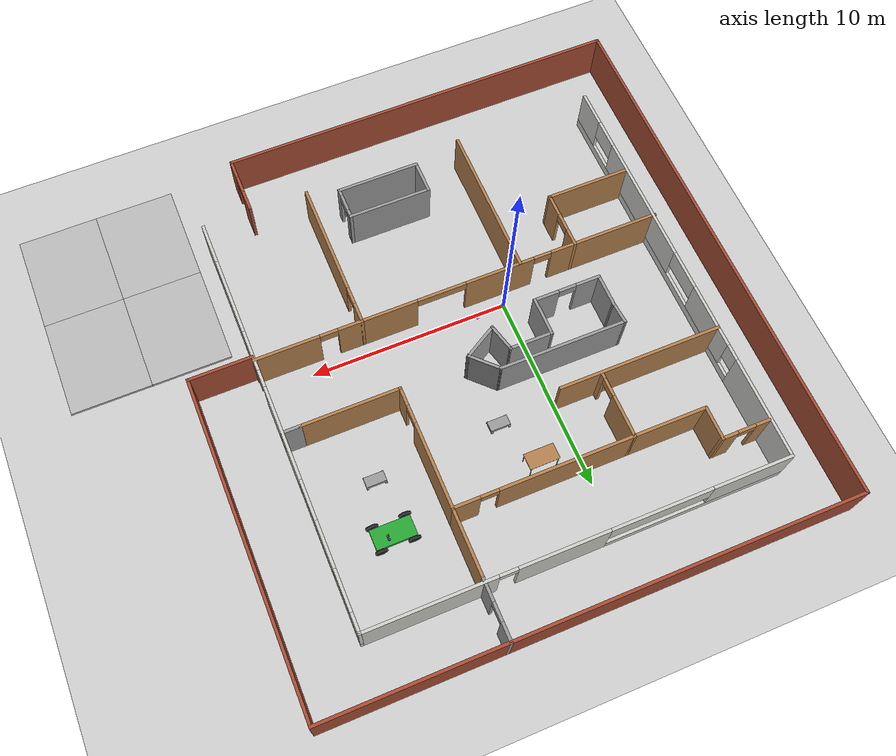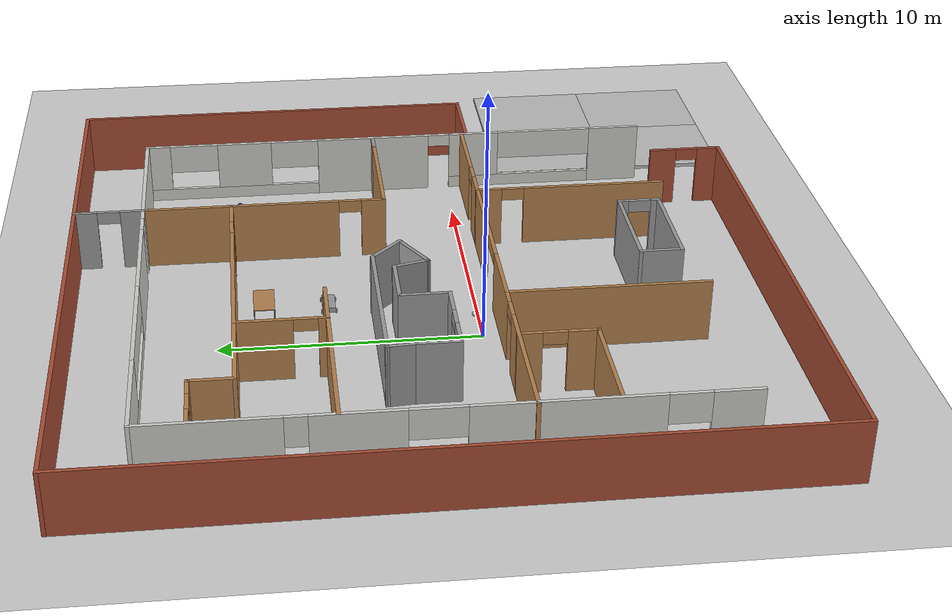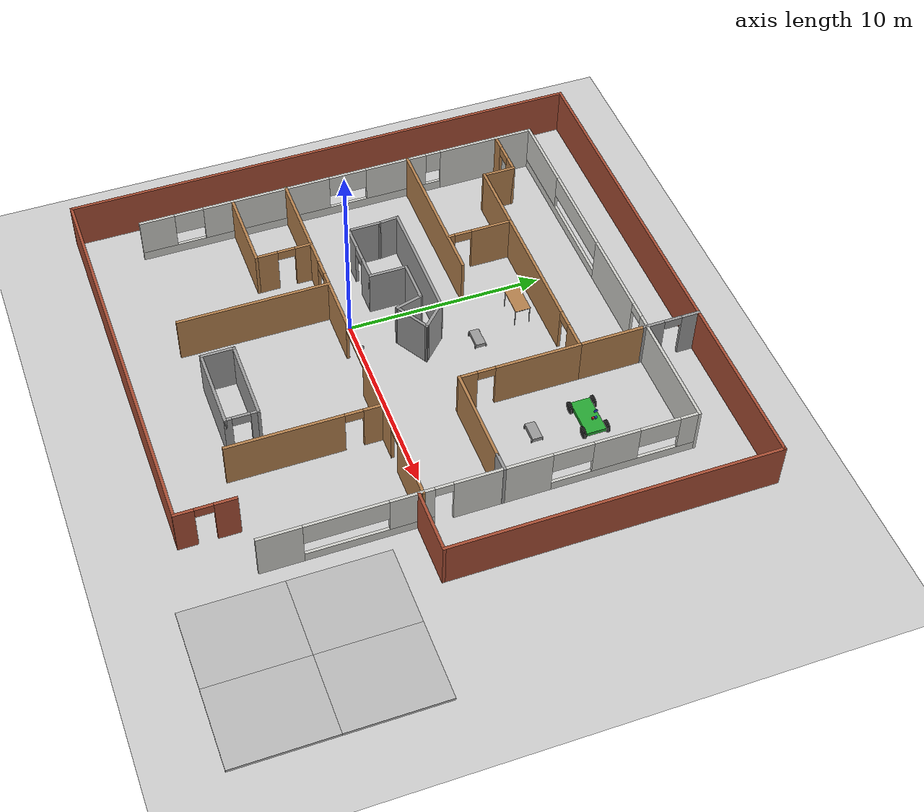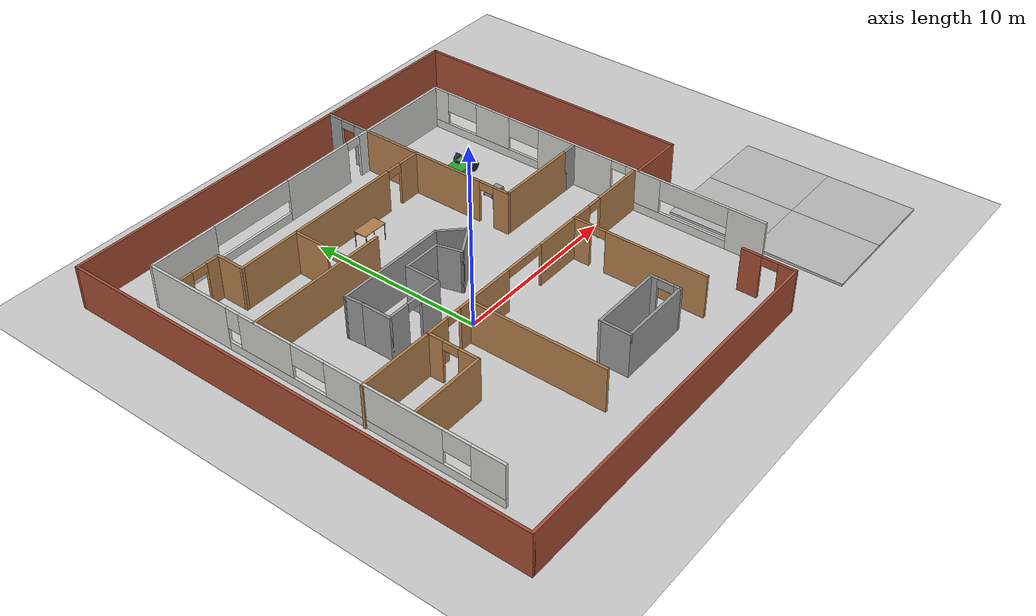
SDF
<sdf version="1.6">
 <world name="default">
  <plugin name="hello" filename="libhello.so"/>
  <light name="sun" type="directional">
   <pose>0 0 10 0 -0 0</pose>
   <diffuse>0.8 0.8 0.8 1</diffuse>
   <specular>0.2 0.2 0.2 1</specular>
   <attenuation>
    <range>1000</range>
    <constant>0.9</constant>
    <linear>0.01</linear>
    <quadratic>0.001</quadratic>
   </attenuation>
   <direction>-0.5 0.1 -0.9</direction>
  </light>
  <model name="ground_plane">
   <static>1</static>
   <link name="link">
    <collision name="collision">
     <geometry><plane><normal>0 0 1</normal><size>1000 1000</size></plane></geometry>
     <surface>
      <contact><collide_bitmask>65535</collide_bitmask></contact>
      <friction><ode><mu>100</mu><mu2>50</mu2></ode></friction>
     </surface>
    </collision>
    <visual name="visual">
     <cast_shadows>0</cast_shadows>
     <geometry><plane><normal>0 0 1</normal><size>1000 1000</size></plane></geometry>
     <material>
      <script><uri>file://media/materials/scripts/gazebo.material</uri><name>Gazebo/Grey</name></script>
     </material>
    </visual>
   </link>
  </model>
  <gravity>0 0 -9.8</gravity>
  <magnetic_field>6e-06 2.3e-05 -4.2e-05</magnetic_field>
  <atmosphere type="adiabatic"/>
  <physics name="default_physics" default="0" type="ode">
   <max_step_size>0.001</max_step_size>
   <real_time_factor>1</real_time_factor>
   <real_time_update_rate>1000</real_time_update_rate>
  </physics>
  <scene><ambient>0.4 0.4 0.4 1</ambient><background>0.7 0.7 0.7 1</background><shadows>1</shadows></scene>
  <spherical_coordinates>
   <surface_model>EARTH_WGS84</surface_model>
   <latitude_deg>0</latitude_deg>
   <longitude_deg>0</longitude_deg>
   <elevation>0</elevation>
   <heading_deg>0</heading_deg>
  </spherical_coordinates>
  <model name="myWorld">
   <pose>2.63259 2.04676 0 0 -0 0</pose>
   <link name="Wall_0">
    <pose>-10.7788 0.167812 0 0 0 -1.5708</pose>
    <visual name="Wall_0_Visual_0">
     <pose>-8.06574 0 1.25 0 -0 0</pose>
     <geometry><box><size>5.11851 0.15 2.5</size></box></geometry>
     <material>
      <script><uri>file://media/materials/scripts/gazebo.material</uri><name>Gazebo/CeilingTiled</name></script>
      <ambient>0.435294 0.796078 0.67451 1</ambient>
     </material>
     <meta><layer>0</layer></meta>
    </visual>
    <collision name="Wall_0_Collision_0">
     <geometry><box><size>5.11851 0.15 2.5</size></box></geometry>
     <pose>-8.06574 0 1.25 0 -0 0</pose>
    </collision>
    <visual name="Wall_0_Visual_1">
     <pose>2.55926 0 0.25 0 -0 0</pose>
     <geometry><box><size>16.1315 0.15 0.5</size></box></geometry>
     <material>
      <script><uri>file://media/materials/scripts/gazebo.material</uri><name>Gazebo/CeilingTiled</name></script>
      <ambient>0.435294 0.796078 0.67451 1</ambient>
     </material>
     <meta><layer>0</layer></meta>
    </visual>
    <collision name="Wall_0_Collision_1">
     <geometry><box><size>16.1315 0.15 0.5</size></box></geometry>
     <pose>2.55926 0 0.25 0 -0 0</pose>
    </collision>
    <visual name="Wall_0_Visual_2">
     <pose>-3.05702 0 1.5 0 -0 0</pose>
     <geometry><box><size>3.29893 0.15 2</size></box></geometry>
     <material>
      <script><uri>file://media/materials/scripts/gazebo.material</uri><name>Gazebo/CeilingTiled</name></script>
      <ambient>0.435294 0.796078 0.67451 1</ambient>
     </material>
     <meta><layer>0</layer></meta>
    </visual>
    <collision name="Wall_0_Collision_2">
     <geometry><box><size>3.29893 0.15 2</size></box></geometry>
     <pose>-3.05702 0 1.5 0 -0 0</pose>
    </collision>
    <visual name="Wall_0_Visual_3">
     <pose>3.95094 0 1.5 0 -0 0</pose>
     <geometry><box><size>6.717 0.15 2</size></box></geometry>
     <material>
      <script><uri>file://media/materials/scripts/gazebo.material</uri><name>Gazebo/CeilingTiled</name></script>
      <ambient>0.435294 0.796078 0.67451 1</ambient>
     </material>
     <meta><layer>0</layer></meta>
    </visual>
    <collision name="Wall_0_Collision_3">
     <geometry><box><size>6.717 0.15 2</size></box></geometry>
     <pose>3.95094 0 1.5 0 -0 0</pose>
    </collision>
    <visual name="Wall_0_Visual_4">
     <pose>9.71722 0 1.5 0 -0 0</pose>
     <geometry><box><size>1.81556 0.15 2</size></box></geometry>
     <material>
      <script><uri>file://media/materials/scripts/gazebo.material</uri><name>Gazebo/CeilingTiled</name></script>
      <ambient>0.435294 0.796078 0.67451 1</ambient>
     </material>
     <meta><layer>0</layer></meta>
    </visual>
    <collision name="Wall_0_Collision_4">
     <geometry><box><size>1.81556 0.15 2</size></box></geometry>
     <pose>9.71722 0 1.5 0 -0 0</pose>
    </collision>
    <visual name="Wall_0_Visual_5">
     <pose>-5.10649 0 1.9 0 -0 0</pose>
     <geometry><box><size>0.8 0.15 1.2</size></box></geometry>
     <material>
      <script><uri>file://media/materials/scripts/gazebo.material</uri><name>Gazebo/CeilingTiled</name></script>
      <ambient>0.435294 0.796078 0.67451 1</ambient>
     </material>
     <meta><layer>0</layer></meta>
    </visual>
    <collision name="Wall_0_Collision_5">
     <geometry><box><size>0.8 0.15 1.2</size></box></geometry>
     <pose>-5.10649 0 1.9 0 -0 0</pose>
    </collision>
    <visual name="Wall_0_Visual_6">
     <pose>-0.407555 0 1.9 0 -0 0</pose>
     <geometry><box><size>2 0.15 1.2</size></box></geometry>
     <material>
      <script><uri>file://media/materials/scripts/gazebo.material</uri><name>Gazebo/CeilingTiled</name></script>
      <ambient>0.435294 0.796078 0.67451 1</ambient>
     </material>
     <meta><layer>0</layer></meta>
    </visual>
    <collision name="Wall_0_Collision_6">
     <geometry><box><size>2 0.15 1.2</size></box></geometry>
     <pose>-0.407555 0 1.9 0 -0 0</pose>
    </collision>
    <visual name="Wall_0_Visual_7">
     <pose>8.05945 0 1.9 0 -0 0</pose>
     <geometry><box><size>1.5 0.15 1.2</size></box></geometry>
     <material>
      <script><uri>file://media/materials/scripts/gazebo.material</uri><name>Gazebo/CeilingTiled</name></script>
      <ambient>0.435294 0.796078 0.67451 1</ambient>
     </material>
     <meta><layer>0</layer></meta>
    </visual>
    <collision name="Wall_0_Collision_7">
     <geometry><box><size>1.5 0.15 1.2</size></box></geometry>
     <pose>8.05945 0 1.9 0 -0 0</pose>
    </collision>
   </link>
   <link name="Wall_10">
    <collision name="Wall_10_Collision">
     <geometry><box><size>7.75 0.15 2.5</size></box></geometry>
     <pose>0 0 1.25 0 -0 0</pose>
    </collision>
    <visual name="Wall_10_Visual">
     <pose>0 0 1.25 0 -0 0</pose>
     <geometry><box><size>7.75 0.15 2.5</size></box></geometry>
     <material>
      <script><uri>file://media/materials/scripts/gazebo.material</uri><name>Gazebo/Wood</name></script>
      <ambient>1 1 1 1</ambient>
     </material>
     <meta><layer>0</layer></meta>
    </visual>
    <pose>-3.63916 -6.5453 0 0 0 -1.5708</pose>
   </link>
   <link name="Wall_109">
    <pose>4.125 12 0 0 -0 1.5708</pose>
    <visual name="Wall_109_Visual_0">
     <pose>-0.939554 0 1.25 0 -0 0</pose>
     <geometry><box><size>1.12089 0.15 2.5</size></box></geometry>
     <material>
      <script><uri>file://media/materials/scripts/gazebo.material</uri><name>Gazebo/Grey</name></script>
      <ambient>1 1 1 1</ambient>
     </material>
     <meta><layer>0</layer></meta>
    </visual>
    <collision name="Wall_109_Collision_0">
     <geometry><box><size>1.12089 0.15 2.5</size></box></geometry>
     <pose>-0.939554 0 1.25 0 -0 0</pose>
    </collision>
    <visual name="Wall_109_Visual_1">
     <pose>1.01045 0 1.25 0 -0 0</pose>
     <geometry><box><size>0.979109 0.15 2.5</size></box></geometry>
     <material>
      <script><uri>file://media/materials/scripts/gazebo.material</uri><name>Gazebo/Grey</name></script>
      <ambient>1 1 1 1</ambient>
     </material>
     <meta><layer>0</layer></meta>
    </visual>
    <collision name="Wall_109_Collision_1">
     <geometry><box><size>0.979109 0.15 2.5</size></box></geometry>
     <pose>1.01045 0 1.25 0 -0 0</pose>
    </collision>
    <visual name="Wall_109_Visual_2">
     <pose>0.070891 0 2.25 0 -0 0</pose>
     <geometry><box><size>0.9 0.15 0.5</size></box></geometry>
     <material>
      <script><uri>file://media/materials/scripts/gazebo.material</uri><name>Gazebo/Grey</name></script>
      <ambient>1 1 1 1</ambient>
     </material>
     <meta><layer>0</layer></meta>
    </visual>
    <collision name="Wall_109_Collision_2">
     <geometry><box><size>0.9 0.15 0.5</size></box></geometry>
     <pose>0.070891 0 2.25 0 -0 0</pose>
    </collision>
   </link>
   <link name="Wall_110">
    <collision name="Wall_110_Collision">
     <geometry><box><size>17.25 0.15 2.5</size></box></geometry>
     <pose>0 0 1.25 0 -0 0</pose>
    </collision>
    <visual name="Wall_110_Visual">
     <pose>0 0 1.25 0 -0 0</pose>
     <geometry><box><size>17.25 0.15 2.5</size></box></geometry>
     <material>
      <script><uri>file://media/materials/scripts/gazebo.material</uri><name>Gazebo/Bricks</name></script>
      <ambient>1 1 1 1</ambient>
     </material>
     <meta><layer>0</layer></meta>
    </visual>
    <pose>-4.425 13.425 0 0 -0 3.14159</pose>
   </link>
   <link name="Wall_111">
    <collision name="Wall_111_Collision">
     <geometry><box><size>27 0.15 2.5</size></box></geometry>
     <pose>0 0 1.25 0 -0 0</pose>
    </collision>
    <visual name="Wall_111_Visual">
     <pose>0 0 1.25 0 -0 0</pose>
     <geometry><box><size>27 0.15 2.5</size></box></geometry>
     <material>
      <script><uri>file://media/materials/scripts/gazebo.material</uri><name>Gazebo/Bricks</name></script>
      <ambient>1 1 1 1</ambient>
     </material>
     <meta><layer>0</layer></meta>
    </visual>
    <pose>-12.975 0 0 0 0 -1.5708</pose>
   </link>
   <link name="Wall_112">
    <collision name="Wall_112_Collision">
     <geometry><box><size>20.5 0.15 2.5</size></box></geometry>
     <pose>0 0 1.25 0 -0 0</pose>
    </collision>
    <visual name="Wall_112_Visual">
     <pose>0 0 1.25 0 -0 0</pose>
     <geometry><box><size>20.5 0.15 2.5</size></box></geometry>
     <material>
      <script><uri>file://media/materials/scripts/gazebo.material</uri><name>Gazebo/Bricks</name></script>
      <ambient>1 1 1 1</ambient>
     </material>
     <meta><layer>0</layer></meta>
    </visual>
    <pose>-2.8 -13.425 0 0 -0 0</pose>
   </link>
   <link name="Wall_113">
    <pose>7.375 -12 0 0 -0 1.5708</pose>
    <visual name="Wall_113_Visual_0">
     <pose>-1.00437 0 1.25 0 -0 0</pose>
     <geometry><box><size>0.991263 0.15 2.5</size></box></geometry>
     <material>
      <script><uri>file://media/materials/scripts/gazebo.material</uri><name>Gazebo/Bricks</name></script>
      <ambient>1 1 1 1</ambient>
     </material>
     <meta><layer>0</layer></meta>
    </visual>
    <collision name="Wall_113_Collision_0">
     <geometry><box><size>0.991263 0.15 2.5</size></box></geometry>
     <pose>-1.00437 0 1.25 0 -0 0</pose>
    </collision>
    <visual name="Wall_113_Visual_1">
     <pose>0.945632 0 1.25 0 -0 0</pose>
     <geometry><box><size>1.10874 0.15 2.5</size></box></geometry>
     <material>
      <script><uri>file://media/materials/scripts/gazebo.material</uri><name>Gazebo/Bricks</name></script>
      <ambient>1 1 1 1</ambient>
     </material>
     <meta><layer>0</layer></meta>
    </visual>
    <collision name="Wall_113_Collision_1">
     <geometry><box><size>1.10874 0.15 2.5</size></box></geometry>
     <pose>0.945632 0 1.25 0 -0 0</pose>
    </collision>
    <visual name="Wall_113_Visual_2">
     <pose>-0.058737 0 2.25 0 -0 0</pose>
     <geometry><box><size>0.9 0.15 0.5</size></box></geometry>
     <material>
      <script><uri>file://media/materials/scripts/gazebo.material</uri><name>Gazebo/Bricks</name></script>
      <ambient>1 1 1 1</ambient>
     </material>
     <meta><layer>0</layer></meta>
    </visual>
    <collision name="Wall_113_Collision_2">
     <geometry><box><size>0.9 0.15 0.5</size></box></geometry>
     <pose>-0.058737 0 2.25 0 -0 0</pose>
    </collision>
   </link>
   <link name="Wall_115">
    <collision name="Wall_115_Collision">
     <geometry><box><size>9 0.15 2.5</size></box></geometry>
     <pose>0 0 1.25 0 -0 0</pose>
    </collision>
    <visual name="Wall_115_Visual">
     <pose>0 0 1.25 0 -0 0</pose>
     <geometry><box><size>9 0.15 2.5</size></box></geometry>
     <material>
      <script><uri>file://media/materials/scripts/gazebo.material</uri><name>Gazebo/Bricks</name></script>
      <ambient>1 1 1 1</ambient>
     </material>
     <meta><layer>0</layer></meta>
    </visual>
    <pose>8.55 13.425 0 0 -0 0</pose>
   </link>
   <link name="Wall_116">
    <collision name="Wall_116_Collision">
     <geometry><box><size>16.5 0.15 2.5</size></box></geometry>
     <pose>0 0 1.25 0 -0 0</pose>
    </collision>
    <visual name="Wall_116_Visual">
     <pose>0 0 1.25 0 -0 0</pose>
     <geometry><box><size>16.5 0.15 2.5</size></box></geometry>
     <material>
      <script><uri>file://media/materials/scripts/gazebo.material</uri><name>Gazebo/Bricks</name></script>
      <ambient>1 1 1 1</ambient>
     </material>
     <meta><layer>0</layer></meta>
    </visual>
    <pose>12.975 5.25 0 0 0 -1.5708</pose>
   </link>
   <link name="Wall_117">
    <collision name="Wall_117_Collision">
     <geometry><box><size>3.25 0.15 2.5</size></box></geometry>
     <pose>0 0 1.25 0 -0 0</pose>
    </collision>
    <visual name="Wall_117_Visual">
     <pose>0 0 1.25 0 -0 0</pose>
     <geometry><box><size>3.25 0.15 2.5</size></box></geometry>
     <material>
      <script><uri>file://media/materials/scripts/gazebo.material</uri><name>Gazebo/Bricks</name></script>
      <ambient>1 1 1 1</ambient>
     </material>
     <meta><layer>0</layer></meta>
    </visual>
    <pose>11.425 -2.925 0 0 -0 3.14159</pose>
   </link>
   <link name="Wall_12">
    <collision name="Wall_12_Collision">
     <geometry><box><size>8.25 0.15 2.5</size></box></geometry>
     <pose>0 0 1.25 0 -0 0</pose>
    </collision>
    <visual name="Wall_12_Visual">
     <pose>0 0 1.25 0 -0 0</pose>
     <geometry><box><size>8.25 0.15 2.5</size></box></geometry>
     <material>
      <script><uri>file://media/materials/scripts/gazebo.material</uri><name>Gazebo/Wood</name></script>
      <ambient>1 1 1 1</ambient>
     </material>
     <meta><layer>0</layer></meta>
    </visual>
    <pose>-6.72078 3.875 0 0 -0 0</pose>
   </link>
   <link name="Wall_14">
    <pose>-4.725 5.55 0 0 -0 1.5708</pose>
    <visual name="Wall_14_Visual_0">
     <pose>-1.54025 0 1.25 0 -0 0</pose>
     <geometry><box><size>0.419489 0.15 2.5</size></box></geometry>
     <material>
      <script><uri>file://media/materials/scripts/gazebo.material</uri><name>Gazebo/Wood</name></script>
      <ambient>1 1 1 1</ambient>
     </material>
     <meta><layer>0</layer></meta>
    </visual>
    <collision name="Wall_14_Collision_0">
     <geometry><box><size>0.419489 0.15 2.5</size></box></geometry>
     <pose>-1.54025 0 1.25 0 -0 0</pose>
    </collision>
    <visual name="Wall_14_Visual_1">
     <pose>0.659745 0 1.25 0 -0 0</pose>
     <geometry><box><size>2.18051 0.15 2.5</size></box></geometry>
     <material>
      <script><uri>file://media/materials/scripts/gazebo.material</uri><name>Gazebo/Wood</name></script>
      <ambient>1 1 1 1</ambient>
     </material>
     <meta><layer>0</layer></meta>
    </visual>
    <collision name="Wall_14_Collision_1">
     <geometry><box><size>2.18051 0.15 2.5</size></box></geometry>
     <pose>0.659745 0 1.25 0 -0 0</pose>
    </collision>
    <visual name="Wall_14_Visual_2">
     <pose>-0.880511 0 2.25 0 -0 0</pose>
     <geometry><box><size>0.9 0.15 0.5</size></box></geometry>
     <material>
      <script><uri>file://media/materials/scripts/gazebo.material</uri><name>Gazebo/Wood</name></script>
      <ambient>1 1 1 1</ambient>
     </material>
     <meta><layer>0</layer></meta>
    </visual>
    <collision name="Wall_14_Collision_2">
     <geometry><box><size>0.9 0.15 0.5</size></box></geometry>
     <pose>-0.880511 0 2.25 0 -0 0</pose>
    </collision>
   </link>
   <link name="Wall_15">
    <pose>-0.299999 7.225 0 0 -0 0</pose>
    <visual name="Wall_15_Visual_0">
     <pose>-1.14864 0 1.25 0 -0 0</pose>
     <geometry><box><size>6.70272 0.15 2.5</size></box></geometry>
     <material>
      <script><uri>file://media/materials/scripts/gazebo.material</uri><name>Gazebo/Wood</name></script>
      <ambient>1 1 1 1</ambient>
     </material>
     <meta><layer>0</layer></meta>
    </visual>
    <collision name="Wall_15_Collision_0">
     <geometry><box><size>6.70272 0.15 2.5</size></box></geometry>
     <pose>-1.14864 0 1.25 0 -0 0</pose>
    </collision>
    <visual name="Wall_15_Visual_1">
     <pose>3.80136 0 1.25 0 -0 0</pose>
     <geometry><box><size>1.39728 0.15 2.5</size></box></geometry>
     <material>
      <script><uri>file://media/materials/scripts/gazebo.material</uri><name>Gazebo/Wood</name></script>
      <ambient>1 1 1 1</ambient>
     </material>
     <meta><layer>0</layer></meta>
    </visual>
    <collision name="Wall_15_Collision_1">
     <geometry><box><size>1.39728 0.15 2.5</size></box></geometry>
     <pose>3.80136 0 1.25 0 -0 0</pose>
    </collision>
    <visual name="Wall_15_Visual_2">
     <pose>2.65272 0 2.25 0 -0 0</pose>
     <geometry><box><size>0.9 0.15 0.5</size></box></geometry>
     <material>
      <script><uri>file://media/materials/scripts/gazebo.material</uri><name>Gazebo/Wood</name></script>
      <ambient>1 1 1 1</ambient>
     </material>
     <meta><layer>0</layer></meta>
    </visual>
    <collision name="Wall_15_Collision_2">
     <geometry><box><size>0.9 0.15 0.5</size></box></geometry>
     <pose>2.65272 0 2.25 0 -0 0</pose>
    </collision>
   </link>
   <link name="Wall_16">
    <pose>4.125 4.175 0 0 0 -1.5708</pose>
    <visual name="Wall_16_Visual_0">
     <pose>-0.941433 0 1.25 0 -0 0</pose>
     <geometry><box><size>4.36714 0.15 2.5</size></box></geometry>
     <material>
      <script><uri>file://media/materials/scripts/gazebo.material</uri><name>Gazebo/Wood</name></script>
      <ambient>1 1 1 1</ambient>
     </material>
     <meta><layer>0</layer></meta>
    </visual>
    <collision name="Wall_16_Collision_0">
     <geometry><box><size>4.36714 0.15 2.5</size></box></geometry>
     <pose>-0.941433 0 1.25 0 -0 0</pose>
    </collision>
    <visual name="Wall_16_Visual_1">
     <pose>2.63357 0 1.25 0 -0 0</pose>
     <geometry><box><size>0.982865 0.15 2.5</size></box></geometry>
     <material>
      <script><uri>file://media/materials/scripts/gazebo.material</uri><name>Gazebo/Wood</name></script>
      <ambient>1 1 1 1</ambient>
     </material>
     <meta><layer>0</layer></meta>
    </visual>
    <collision name="Wall_16_Collision_1">
     <geometry><box><size>0.982865 0.15 2.5</size></box></geometry>
     <pose>2.63357 0 1.25 0 -0 0</pose>
    </collision>
    <visual name="Wall_16_Visual_2">
     <pose>1.69213 0 2.25 0 -0 0</pose>
     <geometry><box><size>0.9 0.15 0.5</size></box></geometry>
     <material>
      <script><uri>file://media/materials/scripts/gazebo.material</uri><name>Gazebo/Wood</name></script>
      <ambient>1 1 1 1</ambient>
     </material>
     <meta><layer>0</layer></meta>
    </visual>
    <collision name="Wall_16_Collision_2">
     <geometry><box><size>0.9 0.15 0.5</size></box></geometry>
     <pose>1.69213 0 2.25 0 -0 0</pose>
    </collision>
   </link>
   <link name="Wall_17">
    <collision name="Wall_17_Collision">
     <geometry><box><size>5 0.15 2.5</size></box></geometry>
     <pose>0 0 1.25 0 -0 0</pose>
    </collision>
    <visual name="Wall_17_Visual">
     <pose>0 0 1.25 0 -0 0</pose>
     <geometry><box><size>5 0.15 2.5</size></box></geometry>
     <material>
      <script><uri>file://media/materials/scripts/gazebo.material</uri><name>Gazebo/Wood</name></script>
      <ambient>1 1 1 1</ambient>
     </material>
     <meta><layer>0</layer></meta>
    </visual>
    <pose>6.55 1.125 0 0 -0 0</pose>
   </link>
   <link name="Wall_18">
    <collision name="Wall_18_Collision">
     <geometry><box><size>1 0.15 2.5</size></box></geometry>
     <pose>0 0 1.25 0 -0 0</pose>
    </collision>
    <visual name="Wall_18_Visual">
     <pose>0 0 1.25 0 -0 0</pose>
     <geometry><box><size>1 0.15 2.5</size></box></geometry>
     <material>
      <script><uri>file://media/materials/scripts/gazebo.material</uri><name>Gazebo/Grey</name></script>
      <ambient>1 1 1 1</ambient>
     </material>
     <meta><layer>0</layer></meta>
    </visual>
    <pose>9.4 1.125 0 0 -0 0</pose>
   </link>
   <link name="Wall_2">
    <pose>9.82118 0.167812 0 0 -0 1.5708</pose>
    <visual name="Wall_2_Visual_0">
     <pose>-9.55148 0 1.25 0 -0 0</pose>
     <geometry><box><size>2.14703 0.15 2.5</size></box></geometry>
     <material>
      <script><uri>file://media/materials/scripts/gazebo.material</uri><name>Gazebo/CeilingTiled</name></script>
      <ambient>0.435294 0.796078 0.67451 1</ambient>
     </material>
     <meta><layer>0</layer></meta>
    </visual>
    <collision name="Wall_2_Collision_0">
     <geometry><box><size>2.14703 0.15 2.5</size></box></geometry>
     <pose>-9.55148 0 1.25 0 -0 0</pose>
    </collision>
    <visual name="Wall_2_Visual_1">
     <pose>0.932508 0 1.25 0 -0 0</pose>
     <geometry><box><size>4.76615 0.15 2.5</size></box></geometry>
     <material>
      <script><uri>file://media/materials/scripts/gazebo.material</uri><name>Gazebo/CeilingTiled</name></script>
      <ambient>0.435294 0.796078 0.67451 1</ambient>
     </material>
     <meta><layer>0</layer></meta>
    </visual>
    <collision name="Wall_2_Collision_1">
     <geometry><box><size>4.76615 0.15 2.5</size></box></geometry>
     <pose>0.932508 0 1.25 0 -0 0</pose>
    </collision>
    <visual name="Wall_2_Visual_2">
     <pose>-5.41427 0 0.25 0 -0 0</pose>
     <geometry><box><size>6.1274 0.15 0.5</size></box></geometry>
     <material>
      <script><uri>file://media/materials/scripts/gazebo.material</uri><name>Gazebo/CeilingTiled</name></script>
      <ambient>0.435294 0.796078 0.67451 1</ambient>
     </material>
     <meta><layer>0</layer></meta>
    </visual>
    <collision name="Wall_2_Collision_2">
     <geometry><box><size>6.1274 0.15 0.5</size></box></geometry>
     <pose>-5.41427 0 0.25 0 -0 0</pose>
    </collision>
    <visual name="Wall_2_Visual_3">
     <pose>6.97029 0 0.25 0 -0 0</pose>
     <geometry><box><size>7.30942 0.15 0.5</size></box></geometry>
     <material>
      <script><uri>file://media/materials/scripts/gazebo.material</uri><name>Gazebo/CeilingTiled</name></script>
      <ambient>0.435294 0.796078 0.67451 1</ambient>
     </material>
     <meta><layer>0</layer></meta>
    </visual>
    <collision name="Wall_2_Collision_3">
     <geometry><box><size>7.30942 0.15 0.5</size></box></geometry>
     <pose>6.97029 0 0.25 0 -0 0</pose>
    </collision>
    <visual name="Wall_2_Visual_4">
     <pose>-3.41427 0 1.5 0 -0 0</pose>
     <geometry><box><size>2.1274 0.15 2</size></box></geometry>
     <material>
      <script><uri>file://media/materials/scripts/gazebo.material</uri><name>Gazebo/CeilingTiled</name></script>
      <ambient>0.435294 0.796078 0.67451 1</ambient>
     </material>
     <meta><layer>0</layer></meta>
    </visual>
    <collision name="Wall_2_Collision_4">
     <geometry><box><size>2.1274 0.15 2</size></box></geometry>
     <pose>-3.41427 0 1.5 0 -0 0</pose>
    </collision>
    <visual name="Wall_2_Visual_5">
     <pose>-3.41427 0 1.5 0 -0 0</pose>
     <geometry><box><size>2.1274 0.15 2</size></box></geometry>
     <material>
      <script><uri>file://media/materials/scripts/gazebo.material</uri><name>Gazebo/CeilingTiled</name></script>
      <ambient>0.435294 0.796078 0.67451 1</ambient>
     </material>
     <meta><layer>0</layer></meta>
    </visual>
    <collision name="Wall_2_Collision_5">
     <geometry><box><size>2.1274 0.15 2</size></box></geometry>
     <pose>-3.41427 0 1.5 0 -0 0</pose>
    </collision>
    <visual name="Wall_2_Visual_6">
     <pose>6.45568 0 1.5 0 -0 0</pose>
     <geometry><box><size>2.2802 0.15 2</size></box></geometry>
     <material>
      <script><uri>file://media/materials/scripts/gazebo.material</uri><name>Gazebo/CeilingTiled</name></script>
      <ambient>0.435294 0.796078 0.67451 1</ambient>
     </material>
     <meta><layer>0</layer></meta>
    </visual>
    <collision name="Wall_2_Collision_6">
     <geometry><box><size>2.2802 0.15 2</size></box></geometry>
     <pose>6.45568 0 1.5 0 -0 0</pose>
    </collision>
    <visual name="Wall_2_Visual_7">
     <pose>10.1104 0 1.5 0 -0 0</pose>
     <geometry><box><size>1.02922 0.15 2</size></box></geometry>
     <material>
      <script><uri>file://media/materials/scripts/gazebo.material</uri><name>Gazebo/CeilingTiled</name></script>
      <ambient>0.435294 0.796078 0.67451 1</ambient>
     </material>
     <meta><layer>0</layer></meta>
    </visual>
    <collision name="Wall_2_Collision_7">
     <geometry><box><size>1.02922 0.15 2</size></box></geometry>
     <pose>10.1104 0 1.5 0 -0 0</pose>
    </collision>
    <visual name="Wall_2_Visual_8">
     <pose>-6.47797 0 1.9 0 -0 0</pose>
     <geometry><box><size>4 0.15 1.2</size></box></geometry>
     <material>
      <script><uri>file://media/materials/scripts/gazebo.material</uri><name>Gazebo/CeilingTiled</name></script>
      <ambient>0.435294 0.796078 0.67451 1</ambient>
     </material>
     <meta><layer>0</layer></meta>
    </visual>
    <collision name="Wall_2_Collision_8">
     <geometry><box><size>4 0.15 1.2</size></box></geometry>
     <pose>-6.47797 0 1.9 0 -0 0</pose>
    </collision>
    <visual name="Wall_2_Visual_9">
     <pose>4.31558 0 1.9 0 -0 0</pose>
     <geometry><box><size>2 0.15 1.2</size></box></geometry>
     <material>
      <script><uri>file://media/materials/scripts/gazebo.material</uri><name>Gazebo/CeilingTiled</name></script>
      <ambient>0.435294 0.796078 0.67451 1</ambient>
     </material>
     <meta><layer>0</layer></meta>
    </visual>
    <collision name="Wall_2_Collision_9">
     <geometry><box><size>2 0.15 1.2</size></box></geometry>
     <pose>4.31558 0 1.9 0 -0 0</pose>
    </collision>
    <visual name="Wall_2_Visual_10">
     <pose>8.59578 0 1.9 0 -0 0</pose>
     <geometry><box><size>2 0.15 1.2</size></box></geometry>
     <material>
      <script><uri>file://media/materials/scripts/gazebo.material</uri><name>Gazebo/CeilingTiled</name></script>
      <ambient>0.435294 0.796078 0.67451 1</ambient>
     </material>
     <meta><layer>0</layer></meta>
    </visual>
    <collision name="Wall_2_Collision_10">
     <geometry><box><size>2 0.15 1.2</size></box></geometry>
     <pose>8.59578 0 1.9 0 -0 0</pose>
    </collision>
    <visual name="Wall_2_Visual_11">
     <pose>-1.90057 0 2.25 0 -0 0</pose>
     <geometry><box><size>0.9 0.15 0.5</size></box></geometry>
     <material>
      <script><uri>file://media/materials/scripts/gazebo.material</uri><name>Gazebo/CeilingTiled</name></script>
      <ambient>0.435294 0.796078 0.67451 1</ambient>
     </material>
     <meta><layer>0</layer></meta>
    </visual>
    <collision name="Wall_2_Collision_11">
     <geometry><box><size>0.9 0.15 0.5</size></box></geometry>
     <pose>-1.90057 0 2.25 0 -0 0</pose>
    </collision>
    <visual name="Wall_2_Visual_12">
     <pose>-1.90057 0 2.25 0 -0 0</pose>
     <geometry><box><size>0.9 0.15 0.5</size></box></geometry>
     <material>
      <script><uri>file://media/materials/scripts/gazebo.material</uri><name>Gazebo/CeilingTiled</name></script>
      <ambient>0.435294 0.796078 0.67451 1</ambient>
     </material>
     <meta><layer>0</layer></meta>
    </visual>
    <collision name="Wall_2_Collision_12">
     <geometry><box><size>0.9 0.15 0.5</size></box></geometry>
     <pose>-1.90057 0 2.25 0 -0 0</pose>
    </collision>
   </link>
   <link name="Wall_20">
    <collision name="Wall_20_Collision">
     <geometry><box><size>3.5 0.15 2.5</size></box></geometry>
     <pose>0 0 1.25 0 -0 0</pose>
    </collision>
    <visual name="Wall_20_Visual">
     <pose>0 0 1.25 0 -0 0</pose>
     <geometry><box><size>3.5 0.15 2.5</size></box></geometry>
     <material>
      <script><uri>file://media/materials/scripts/gazebo.material</uri><name>Gazebo/Wood</name></script>
      <ambient>1 1 1 1</ambient>
     </material>
     <meta><layer>0</layer></meta>
    </visual>
    <pose>4.125 8.9 0 0 -0 1.5708</pose>
   </link>
   <link name="Wall_22">
    <collision name="Wall_22_Collision">
     <geometry><box><size>3.75 0.15 2.5</size></box></geometry>
     <pose>0 0 1.25 0 -0 0</pose>
    </collision>
    <visual name="Wall_22_Visual">
     <pose>0 0 1.25 0 -0 0</pose>
     <geometry><box><size>3.75 0.15 2.5</size></box></geometry>
     <material>
      <script><uri>file://media/materials/scripts/gazebo.material</uri><name>Gazebo/Wood</name></script>
      <ambient>1 1 1 1</ambient>
     </material>
     <meta><layer>0</layer></meta>
    </visual>
    <pose>-6.525 7.225 0 0 -0 3.14159</pose>
   </link>
   <link name="Wall_23">
    <collision name="Wall_23_Collision">
     <geometry><box><size>1.75 0.15 2.5</size></box></geometry>
     <pose>0 0 1.25 0 -0 0</pose>
    </collision>
    <visual name="Wall_23_Visual">
     <pose>0 0 1.25 0 -0 0</pose>
     <geometry><box><size>1.75 0.15 2.5</size></box></geometry>
     <material>
      <script><uri>file://media/materials/scripts/gazebo.material</uri><name>Gazebo/Wood</name></script>
      <ambient>1 1 1 1</ambient>
     </material>
     <meta><layer>0</layer></meta>
    </visual>
    <pose>-8.325 8.025 0 0 -0 1.5708</pose>
   </link>
   <link name="Wall_24">
    <pose>-9.5 8.825 0 0 -0 3.14159</pose>
    <visual name="Wall_24_Visual_0">
     <pose>-0.821298 0 1.25 0 -0 0</pose>
     <geometry><box><size>0.857405 0.15 2.5</size></box></geometry>
     <material>
      <script><uri>file://media/materials/scripts/gazebo.material</uri><name>Gazebo/Wood</name></script>
      <ambient>1 1 1 1</ambient>
     </material>
     <meta><layer>0</layer></meta>
    </visual>
    <collision name="Wall_24_Collision_0">
     <geometry><box><size>0.857405 0.15 2.5</size></box></geometry>
     <pose>-0.821298 0 1.25 0 -0 0</pose>
    </collision>
    <visual name="Wall_24_Visual_1">
     <pose>0.878702 0 1.25 0 -0 0</pose>
     <geometry><box><size>0.742595 0.15 2.5</size></box></geometry>
     <material>
      <script><uri>file://media/materials/scripts/gazebo.material</uri><name>Gazebo/Wood</name></script>
      <ambient>1 1 1 1</ambient>
     </material>
     <meta><layer>0</layer></meta>
    </visual>
    <collision name="Wall_24_Collision_1">
     <geometry><box><size>0.742595 0.15 2.5</size></box></geometry>
     <pose>0.878702 0 1.25 0 -0 0</pose>
    </collision>
    <visual name="Wall_24_Visual_2">
     <pose>0.057405 0 2.25 0 -0 0</pose>
     <geometry><box><size>0.9 0.15 0.5</size></box></geometry>
     <material>
      <script><uri>file://media/materials/scripts/gazebo.material</uri><name>Gazebo/Wood</name></script>
      <ambient>1 1 1 1</ambient>
     </material>
     <meta><layer>0</layer></meta>
    </visual>
    <collision name="Wall_24_Collision_2">
     <geometry><box><size>0.9 0.15 0.5</size></box></geometry>
     <pose>0.057405 0 2.25 0 -0 0</pose>
    </collision>
   </link>
   <link name="Wall_26">
    <pose>-6.53335 -4.15281 0 0 0 -1.5708</pose>
    <visual name="Wall_26_Visual_0">
     <pose>-1.03617 0 1.25 0 -0 0</pose>
     <geometry><box><size>0.927669 0.15 2.5</size></box></geometry>
     <material>
      <script><uri>file://media/materials/scripts/gazebo.material</uri><name>Gazebo/Wood</name></script>
      <ambient>1 1 1 1</ambient>
     </material>
     <meta><layer>0</layer></meta>
    </visual>
    <collision name="Wall_26_Collision_0">
     <geometry><box><size>0.927669 0.15 2.5</size></box></geometry>
     <pose>-1.03617 0 1.25 0 -0 0</pose>
    </collision>
    <visual name="Wall_26_Visual_1">
     <pose>0.913835 0 1.25 0 -0 0</pose>
     <geometry><box><size>1.17233 0.15 2.5</size></box></geometry>
     <material>
      <script><uri>file://media/materials/scripts/gazebo.material</uri><name>Gazebo/Wood</name></script>
      <ambient>1 1 1 1</ambient>
     </material>
     <meta><layer>0</layer></meta>
    </visual>
    <collision name="Wall_26_Collision_1">
     <geometry><box><size>1.17233 0.15 2.5</size></box></geometry>
     <pose>0.913835 0 1.25 0 -0 0</pose>
    </collision>
    <visual name="Wall_26_Visual_2">
     <pose>-0.122331 0 2.25 0 -0 0</pose>
     <geometry><box><size>0.9 0.15 0.5</size></box></geometry>
     <material>
      <script><uri>file://media/materials/scripts/gazebo.material</uri><name>Gazebo/Wood</name></script>
      <ambient>1 1 1 1</ambient>
     </material>
     <meta><layer>0</layer></meta>
    </visual>
    <collision name="Wall_26_Collision_2">
     <geometry><box><size>0.9 0.15 0.5</size></box></geometry>
     <pose>-0.122331 0 2.25 0 -0 0</pose>
    </collision>
   </link>
   <link name="Wall_27">
    <collision name="Wall_27_Collision">
     <geometry><box><size>4.25 0.15 2.5</size></box></geometry>
     <pose>0 0 1.25 0 -0 0</pose>
    </collision>
    <visual name="Wall_27_Visual">
     <pose>0 0 1.25 0 -0 0</pose>
     <geometry><box><size>4.25 0.15 2.5</size></box></geometry>
     <material>
      <script><uri>file://media/materials/scripts/gazebo.material</uri><name>Gazebo/Wood</name></script>
      <ambient>1 1 1 1</ambient>
     </material>
     <meta><layer>0</layer></meta>
    </visual>
    <pose>-8.58335 -5.57781 0 0 -0 3.14159</pose>
   </link>
   <link name="Wall_3">
    <pose>-0.478823 10.7178 0 0 -0 3.14159</pose>
    <visual name="Wall_3_Visual_0">
     <pose>-7.15394 0 1.25 0 -0 0</pose>
     <geometry><box><size>6.44212 0.15 2.5</size></box></geometry>
     <material>
      <script><uri>file://media/materials/scripts/gazebo.material</uri><name>Gazebo/CeilingTiled</name></script>
      <ambient>0.435294 0.796078 0.67451 1</ambient>
     </material>
     <meta><layer>0</layer></meta>
    </visual>
    <collision name="Wall_3_Collision_0">
     <geometry><box><size>6.44212 0.15 2.5</size></box></geometry>
     <pose>-7.15394 0 1.25 0 -0 0</pose>
    </collision>
    <visual name="Wall_3_Visual_1">
     <pose>-0.832486 0 1.25 0 -0 0</pose>
     <geometry><box><size>4.40078 0.15 2.5</size></box></geometry>
     <material>
      <script><uri>file://media/materials/scripts/gazebo.material</uri><name>Gazebo/CeilingTiled</name></script>
      <ambient>0.435294 0.796078 0.67451 1</ambient>
     </material>
     <meta><layer>0</layer></meta>
    </visual>
    <collision name="Wall_3_Collision_1">
     <geometry><box><size>4.40078 0.15 2.5</size></box></geometry>
     <pose>-0.832486 0 1.25 0 -0 0</pose>
    </collision>
    <visual name="Wall_3_Visual_2">
     <pose>5.87145 0 0.25 0 -0 0</pose>
     <geometry><box><size>9.0071 0.15 0.5</size></box></geometry>
     <material>
      <script><uri>file://media/materials/scripts/gazebo.material</uri><name>Gazebo/CeilingTiled</name></script>
      <ambient>0.435294 0.796078 0.67451 1</ambient>
     </material>
     <meta><layer>0</layer></meta>
    </visual>
    <collision name="Wall_3_Collision_2">
     <geometry><box><size>9.0071 0.15 0.5</size></box></geometry>
     <pose>5.87145 0 0.25 0 -0 0</pose>
    </collision>
    <visual name="Wall_3_Visual_3">
     <pose>8.37145 0 1.5 0 -0 0</pose>
     <geometry><box><size>4.0071 0.15 2</size></box></geometry>
     <material>
      <script><uri>file://media/materials/scripts/gazebo.material</uri><name>Gazebo/CeilingTiled</name></script>
      <ambient>0.435294 0.796078 0.67451 1</ambient>
     </material>
     <meta><layer>0</layer></meta>
    </visual>
    <collision name="Wall_3_Collision_3">
     <geometry><box><size>4.0071 0.15 2</size></box></geometry>
     <pose>8.37145 0 1.5 0 -0 0</pose>
    </collision>
    <visual name="Wall_3_Visual_4">
     <pose>3.8679 0 1.9 0 -0 0</pose>
     <geometry><box><size>5 0.15 1.2</size></box></geometry>
     <material>
      <script><uri>file://media/materials/scripts/gazebo.material</uri><name>Gazebo/CeilingTiled</name></script>
      <ambient>0.435294 0.796078 0.67451 1</ambient>
     </material>
     <meta><layer>0</layer></meta>
    </visual>
    <collision name="Wall_3_Collision_4">
     <geometry><box><size>5 0.15 1.2</size></box></geometry>
     <pose>3.8679 0 1.9 0 -0 0</pose>
    </collision>
    <visual name="Wall_3_Visual_5">
     <pose>-3.48287 0 2.25 0 -0 0</pose>
     <geometry><box><size>0.9 0.15 0.5</size></box></geometry>
     <material>
      <script><uri>file://media/materials/scripts/gazebo.material</uri><name>Gazebo/CeilingTiled</name></script>
      <ambient>0.435294 0.796078 0.67451 1</ambient>
     </material>
     <meta><layer>0</layer></meta>
    </visual>
    <collision name="Wall_3_Collision_5">
     <geometry><box><size>0.9 0.15 0.5</size></box></geometry>
     <pose>-3.48287 0 2.25 0 -0 0</pose>
    </collision>
   </link>
   <link name="Wall_5">
    <pose>4.50252 -6.52869 0 0 -0 1.5708</pose>
    <visual name="Wall_5_Visual_0">
     <pose>-0.98318 0 1.25 0 -0 0</pose>
     <geometry><box><size>5.78364 0.15 2.5</size></box></geometry>
     <material>
      <script><uri>file://media/materials/scripts/gazebo.material</uri><name>Gazebo/Wood</name></script>
      <ambient>1 1 1 1</ambient>
     </material>
     <meta><layer>0</layer></meta>
    </visual>
    <collision name="Wall_5_Collision_0">
     <geometry><box><size>5.78364 0.15 2.5</size></box></geometry>
     <pose>-0.98318 0 1.25 0 -0 0</pose>
    </collision>
    <visual name="Wall_5_Visual_1">
     <pose>3.34182 0 1.25 0 -0 0</pose>
     <geometry><box><size>1.06636 0.15 2.5</size></box></geometry>
     <material>
      <script><uri>file://media/materials/scripts/gazebo.material</uri><name>Gazebo/Wood</name></script>
      <ambient>1 1 1 1</ambient>
     </material>
     <meta><layer>0</layer></meta>
    </visual>
    <collision name="Wall_5_Collision_1">
     <geometry><box><size>1.06636 0.15 2.5</size></box></geometry>
     <pose>3.34182 0 1.25 0 -0 0</pose>
    </collision>
    <visual name="Wall_5_Visual_2">
     <pose>2.35864 0 2.25 0 -0 0</pose>
     <geometry><box><size>0.9 0.15 0.5</size></box></geometry>
     <material>
      <script><uri>file://media/materials/scripts/gazebo.material</uri><name>Gazebo/Wood</name></script>
      <ambient>1 1 1 1</ambient>
     </material>
     <meta><layer>0</layer></meta>
    </visual>
    <collision name="Wall_5_Collision_2">
     <geometry><box><size>0.9 0.15 0.5</size></box></geometry>
     <pose>2.35864 0 2.25 0 -0 0</pose>
    </collision>
   </link>
   <link name="Wall_6">
    <pose>7.17752 -2.72869 0 0 -0 0</pose>
    <visual name="Wall_6_Visual_0">
     <pose>-2.10492 0 1.25 0 -0 0</pose>
     <geometry><box><size>1.29015 0.15 2.5</size></box></geometry>
     <material>
      <script><uri>file://media/materials/scripts/gazebo.material</uri><name>Gazebo/Wood</name></script>
      <ambient>1 1 1 1</ambient>
     </material>
     <meta><layer>0</layer></meta>
    </visual>
    <collision name="Wall_6_Collision_0">
     <geometry><box><size>1.29015 0.15 2.5</size></box></geometry>
     <pose>-2.10492 0 1.25 0 -0 0</pose>
    </collision>
    <visual name="Wall_6_Visual_1">
     <pose>1.09508 0 1.25 0 -0 0</pose>
     <geometry><box><size>3.30985 0.15 2.5</size></box></geometry>
     <material>
      <script><uri>file://media/materials/scripts/gazebo.material</uri><name>Gazebo/Wood</name></script>
      <ambient>1 1 1 1</ambient>
     </material>
     <meta><layer>0</layer></meta>
    </visual>
    <collision name="Wall_6_Collision_1">
     <geometry><box><size>3.30985 0.15 2.5</size></box></geometry>
     <pose>1.09508 0 1.25 0 -0 0</pose>
    </collision>
    <visual name="Wall_6_Visual_2">
     <pose>-1.00985 0 2.25 0 -0 0</pose>
     <geometry><box><size>0.9 0.15 0.5</size></box></geometry>
     <material>
      <script><uri>file://media/materials/scripts/gazebo.material</uri><name>Gazebo/Wood</name></script>
      <ambient>1 1 1 1</ambient>
     </material>
     <meta><layer>0</layer></meta>
    </visual>
    <collision name="Wall_6_Collision_2">
     <geometry><box><size>0.9 0.15 0.5</size></box></geometry>
     <pose>-1.00985 0 2.25 0 -0 0</pose>
    </collision>
   </link>
   <link name="Wall_8">
    <pose>-3.17248 -2.72869 0 0 -0 3.14159</pose>
    <visual name="Wall_8_Visual_0">
     <pose>-6.30886 0 1.25 0 -0 0</pose>
     <geometry><box><size>2.88229 0.15 2.5</size></box></geometry>
     <material>
      <script><uri>file://media/materials/scripts/gazebo.material</uri><name>Gazebo/Wood</name></script>
      <ambient>1 1 1 1</ambient>
     </material>
     <meta><layer>0</layer></meta>
    </visual>
    <collision name="Wall_8_Collision_0">
     <geometry><box><size>2.88229 0.15 2.5</size></box></geometry>
     <pose>-6.30886 0 1.25 0 -0 0</pose>
    </collision>
    <visual name="Wall_8_Visual_1">
     <pose>-0.589112 0 1.25 0 -0 0</pose>
     <geometry><box><size>3.5572 0.15 2.5</size></box></geometry>
     <material>
      <script><uri>file://media/materials/scripts/gazebo.material</uri><name>Gazebo/Wood</name></script>
      <ambient>1 1 1 1</ambient>
     </material>
     <meta><layer>0</layer></meta>
    </visual>
    <collision name="Wall_8_Collision_1">
     <geometry><box><size>3.5572 0.15 2.5</size></box></geometry>
     <pose>-0.589112 0 1.25 0 -0 0</pose>
    </collision>
    <visual name="Wall_8_Visual_2">
     <pose>4.91974 0 1.25 0 -0 0</pose>
     <geometry><box><size>5.66051 0.15 2.5</size></box></geometry>
     <material>
      <script><uri>file://media/materials/scripts/gazebo.material</uri><name>Gazebo/Wood</name></script>
      <ambient>1 1 1 1</ambient>
     </material>
     <meta><layer>0</layer></meta>
    </visual>
    <collision name="Wall_8_Collision_2">
     <geometry><box><size>5.66051 0.15 2.5</size></box></geometry>
     <pose>4.91974 0 1.25 0 -0 0</pose>
    </collision>
    <visual name="Wall_8_Visual_3">
     <pose>-3.61771 0 2.25 0 -0 0</pose>
     <geometry><box><size>2.5 0.15 0.5</size></box></geometry>
     <material>
      <script><uri>file://media/materials/scripts/gazebo.material</uri><name>Gazebo/Wood</name></script>
      <ambient>1 1 1 1</ambient>
     </material>
     <meta><layer>0</layer></meta>
    </visual>
    <collision name="Wall_8_Collision_3">
     <geometry><box><size>2.5 0.15 0.5</size></box></geometry>
     <pose>-3.61771 0 2.25 0 -0 0</pose>
    </collision>
    <visual name="Wall_8_Visual_4">
     <pose>1.63949 0 2.25 0 -0 0</pose>
     <geometry><box><size>0.9 0.15 0.5</size></box></geometry>
     <material>
      <script><uri>file://media/materials/scripts/gazebo.material</uri><name>Gazebo/Wood</name></script>
      <ambient>1 1 1 1</ambient>
     </material>
     <meta><layer>0</layer></meta>
    </visual>
    <collision name="Wall_8_Collision_4">
     <geometry><box><size>0.9 0.15 0.5</size></box></geometry>
     <pose>1.63949 0 2.25 0 -0 0</pose>
    </collision>
   </link>
   <static>1</static>
  </model>
  <model name="mybuild">
   <pose>3.5321 -7.00889 0 0 -0 0</pose>
   <link name="Wall_0">
    <collision name="Wall_0_Collision">
     <geometry><box><size>1.75 0.15 2.5</size></box></geometry>
     <pose>0 0 1.25 0 -0 0</pose>
    </collision>
    <visual name="Wall_0_Visual">
     <pose>0 0 1.25 0 -0 0</pose>
     <geometry><box><size>1.75 0.15 2.5</size></box></geometry>
     <material>
      <script><uri>file://media/materials/scripts/gazebo.material</uri><name>Gazebo/Grey</name></script>
      <ambient>1 1 1 1</ambient>
     </material>
     <meta><layer>0</layer></meta>
    </visual>
    <pose>-2.05 0 0 0 0 -1.5708</pose>
   </link>
   <link name="Wall_1">
    <collision name="Wall_1_Collision">
     <geometry><box><size>4.25 0.15 2.5</size></box></geometry>
     <pose>0 0 1.25 0 -0 0</pose>
    </collision>
    <visual name="Wall_1_Visual">
     <pose>0 0 1.25 0 -0 0</pose>
     <geometry><box><size>4.25 0.15 2.5</size></box></geometry>
     <material>
      <script><uri>file://media/materials/scripts/gazebo.material</uri><name>Gazebo/Grey</name></script>
      <ambient>1 1 1 1</ambient>
     </material>
     <meta><layer>0</layer></meta>
    </visual>
    <pose>0 -0.8 0 0 -0 0</pose>
   </link>
   <link name="Wall_2">
    <pose>2.05 0 0 0 -0 1.5708</pose>
    <visual name="Wall_2_Visual_0">
     <pose>-0.6775 0 1.25 0 -0 0</pose>
     <geometry><box><size>0.395 0.15 2.5</size></box></geometry>
     <material>
      <script><uri>file://media/materials/scripts/gazebo.material</uri><name>Gazebo/Grey</name></script>
      <ambient>1 1 1 1</ambient>
     </material>
     <meta><layer>0</layer></meta>
    </visual>
    <collision name="Wall_2_Collision_0">
     <geometry><box><size>0.395 0.15 2.5</size></box></geometry>
     <pose>-0.6775 0 1.25 0 -0 0</pose>
    </collision>
    <visual name="Wall_2_Visual_1">
     <pose>0.6475 0 1.25 0 -0 0</pose>
     <geometry><box><size>0.455 0.15 2.5</size></box></geometry>
     <material>
      <script><uri>file://media/materials/scripts/gazebo.material</uri><name>Gazebo/Grey</name></script>
      <ambient>1 1 1 1</ambient>
     </material>
     <meta><layer>0</layer></meta>
    </visual>
    <collision name="Wall_2_Collision_1">
     <geometry><box><size>0.455 0.15 2.5</size></box></geometry>
     <pose>0.6475 0 1.25 0 -0 0</pose>
    </collision>
    <visual name="Wall_2_Visual_2">
     <pose>-0.03 0 2.25 0 -0 0</pose>
     <geometry><box><size>0.9 0.15 0.5</size></box></geometry>
     <material>
      <script><uri>file://media/materials/scripts/gazebo.material</uri><name>Gazebo/Grey</name></script>
      <ambient>1 1 1 1</ambient>
     </material>
     <meta><layer>0</layer></meta>
    </visual>
    <collision name="Wall_2_Collision_2">
     <geometry><box><size>0.9 0.15 0.5</size></box></geometry>
     <pose>-0.03 0 2.25 0 -0 0</pose>
    </collision>
   </link>
   <link name="Wall_3">
    <collision name="Wall_3_Collision">
     <geometry><box><size>4.25 0.15 2.5</size></box></geometry>
     <pose>0 0 1.25 0 -0 0</pose>
    </collision>
    <visual name="Wall_3_Visual">
     <pose>0 0 1.25 0 -0 0</pose>
     <geometry><box><size>4.25 0.15 2.5</size></box></geometry>
     <material>
      <script><uri>file://media/materials/scripts/gazebo.material</uri><name>Gazebo/Grey</name></script>
      <ambient>1 1 1 1</ambient>
     </material>
     <meta><layer>0</layer></meta>
    </visual>
    <pose>0 0.8 0 0 -0 3.14159</pose>
   </link>
   <static>1</static>
  </model>
  <model name="test1">
   <pose>-0.50116 2.70346 0 0 -0 0</pose>
   <link name="Wall_0">
    <collision name="Wall_0_Collision">
     <geometry><box><size>1.75 0.15 2.5</size></box></geometry>
     <pose>0 0 1.25 0 -0 0</pose>
    </collision>
    <visual name="Wall_0_Visual">
     <pose>0 0 1.25 0 -0 0</pose>
     <geometry><box><size>1.75 0.15 2.5</size></box></geometry>
     <material>
      <script><uri>file://media/materials/scripts/gazebo.material</uri><name>Gazebo/Grey</name></script>
      <ambient>1 1 1 1</ambient>
     </material>
     <meta><layer>0</layer></meta>
    </visual>
    <pose>-3.67354 -0.516718 0 0 0 -1.5708</pose>
   </link>
   <link name="Wall_1">
    <pose>-1.99854 -1.31672 0 0 -0 0</pose>
    <visual name="Wall_1_Visual_0">
     <pose>-1.1075 0 1.25 0 -0 0</pose>
     <geometry><box><size>1.285 0.15 2.5</size></box></geometry>
     <material>
      <script><uri>file://media/materials/scripts/gazebo.material</uri><name>Gazebo/Grey</name></script>
      <ambient>1 1 1 1</ambient>
     </material>
     <meta><layer>0</layer></meta>
    </visual>
    <collision name="Wall_1_Collision_0">
     <geometry><box><size>1.285 0.15 2.5</size></box></geometry>
     <pose>-1.1075 0 1.25 0 -0 0</pose>
    </collision>
    <visual name="Wall_1_Visual_1">
     <pose>1.0925 0 1.25 0 -0 0</pose>
     <geometry><box><size>1.315 0.15 2.5</size></box></geometry>
     <material>
      <script><uri>file://media/materials/scripts/gazebo.material</uri><name>Gazebo/Grey</name></script>
      <ambient>1 1 1 1</ambient>
     </material>
     <meta><layer>0</layer></meta>
    </visual>
    <collision name="Wall_1_Collision_1">
     <geometry><box><size>1.315 0.15 2.5</size></box></geometry>
     <pose>1.0925 0 1.25 0 -0 0</pose>
    </collision>
    <visual name="Wall_1_Visual_2">
     <pose>-0.015 0 2.25 0 -0 0</pose>
     <geometry><box><size>0.9 0.15 0.5</size></box></geometry>
     <material>
      <script><uri>file://media/materials/scripts/gazebo.material</uri><name>Gazebo/Grey</name></script>
      <ambient>1 1 1 1</ambient>
     </material>
     <meta><layer>0</layer></meta>
    </visual>
    <collision name="Wall_1_Collision_2">
     <geometry><box><size>0.9 0.15 0.5</size></box></geometry>
     <pose>-0.015 0 2.25 0 -0 0</pose>
    </collision>
   </link>
   <link name="Wall_2">
    <collision name="Wall_2_Collision">
     <geometry><box><size>2 0.15 2.5</size></box></geometry>
     <pose>0 0 1.25 0 -0 0</pose>
    </collision>
    <visual name="Wall_2_Visual">
     <pose>0 0 1.25 0 -0 0</pose>
     <geometry><box><size>2 0.15 2.5</size></box></geometry>
     <material>
      <script><uri>file://media/materials/scripts/gazebo.material</uri><name>Gazebo/Grey</name></script>
      <ambient>1 1 1 1</ambient>
     </material>
     <meta><layer>0</layer></meta>
    </visual>
    <pose>-0.323542 -0.391719 0 0 -0 1.5708</pose>
   </link>
   <link name="Wall_3">
    <collision name="Wall_3_Collision">
     <geometry><box><size>2.25 0.15 2.5</size></box></geometry>
     <pose>0 0 1.25 0 -0 0</pose>
    </collision>
    <visual name="Wall_3_Visual">
     <pose>0 0 1.25 0 -0 0</pose>
     <geometry><box><size>2.25 0.15 2.5</size></box></geometry>
     <material>
      <script><uri>file://media/materials/scripts/gazebo.material</uri><name>Gazebo/Grey</name></script>
      <ambient>1 1 1 1</ambient>
     </material>
     <meta><layer>0</layer></meta>
    </visual>
    <pose>0.726458 0.533282 0 0 -0 0</pose>
   </link>
   <link name="Wall_4">
    <collision name="Wall_4_Collision">
     <geometry><box><size>1.5 0.15 2.5</size></box></geometry>
     <pose>0 0 1.25 0 -0 0</pose>
    </collision>
    <visual name="Wall_4_Visual">
     <pose>0 0 1.25 0 -0 0</pose>
     <geometry><box><size>1.5 0.15 2.5</size></box></geometry>
     <material>
      <script><uri>file://media/materials/scripts/gazebo.material</uri><name>Gazebo/Grey</name></script>
      <ambient>1 1 1 1</ambient>
     </material>
     <meta><layer>0</layer></meta>
    </visual>
    <pose>1.95116 -0.118718 0 0 0 -1.309</pose>
   </link>
   <link name="Wall_5">
    <collision name="Wall_5_Collision">
     <geometry><box><size>2 0.15 2.5</size></box></geometry>
     <pose>0 0 1.25 0 -0 0</pose>
    </collision>
    <visual name="Wall_5_Visual">
     <pose>0 0 1.25 0 -0 0</pose>
     <geometry><box><size>2 0.15 2.5</size></box></geometry>
     <material>
      <script><uri>file://media/materials/scripts/gazebo.material</uri><name>Gazebo/Grey</name></script>
      <ambient>1 1 1 1</ambient>
     </material>
     <meta><layer>0</layer></meta>
    </visual>
    <pose>2.92694 -0.308218 0 0 -0 0.523599</pose>
   </link>
   <link name="Wall_6">
    <collision name="Wall_6_Collision">
     <geometry><box><size>1.75 0.15 2.5</size></box></geometry>
     <pose>0 0 1.25 0 -0 0</pose>
    </collision>
    <visual name="Wall_6_Visual">
     <pose>0 0 1.25 0 -0 0</pose>
     <geometry><box><size>1.75 0.15 2.5</size></box></geometry>
     <material>
      <script><uri>file://media/materials/scripts/gazebo.material</uri><name>Gazebo/Grey</name></script>
      <ambient>1 1 1 1</ambient>
     </material>
     <meta><layer>0</layer></meta>
    </visual>
    <pose>3.16233 0.719967 0 0 -0 2.35619</pose>
   </link>
   <link name="Wall_7">
    <collision name="Wall_7_Collision">
     <geometry><box><size>6.5 0.15 2.5</size></box></geometry>
     <pose>0 0 1.25 0 -0 0</pose>
    </collision>
    <visual name="Wall_7_Visual">
     <pose>0 0 1.25 0 -0 0</pose>
     <geometry><box><size>6.5 0.15 2.5</size></box></geometry>
     <material>
      <script><uri>file://media/materials/scripts/gazebo.material</uri><name>Gazebo/Grey</name></script>
      <ambient>1 1 1 1</ambient>
     </material>
     <meta><layer>0</layer></meta>
    </visual>
    <pose>-0.57836 1.28565 0 0 -0 3.14159</pose>
   </link>
   <link name="Wall_8">
    <collision name="Wall_8_Collision">
     <geometry><box><size>1.15554 0.15 2.5</size></box></geometry>
     <pose>0 0 1.25 0 -0 0</pose>
    </collision>
    <visual name="Wall_8_Visual">
     <pose>0 0 1.25 0 -0 0</pose>
     <geometry><box><size>1.15554 0.15 2.5</size></box></geometry>
     <material>
      <script><uri>file://media/materials/scripts/gazebo.material</uri><name>Gazebo/Grey</name></script>
      <ambient>1 1 1 1</ambient>
     </material>
     <meta><layer>0</layer></meta>
    </visual>
    <pose>-3.71345 0.784467 0 0 0 -1.49134</pose>
   </link>
   <static>1</static>
  </model>
  <model name="mybot">
   <link name="link_0">
    <pose>-1e-06 2e-06 0.2754 0 -0 0</pose>
    <inertial>
     <mass>1</mass>
     <inertia>
      <ixx>0.166667</ixx>
      <ixy>0</ixy>
      <ixz>0</ixz>
      <iyy>0.166667</iyy>
      <iyz>0</iyz>
      <izz>0.166667</izz>
     </inertia>
    </inertial>
    <visual name="visual">
     <geometry><box><size>1 0.5 0.2</size></box></geometry>
     <material>
      <lighting>1</lighting>
      <script><uri>file://media/materials/scripts/gazebo.material</uri><name>Gazebo/Grey</name></script>
      <shader type="pixel"><normal_map>__default__</normal_map></shader>
      <ambient>0.3 0.3 0.3 1</ambient>
      <diffuse>0.7 0.7 0.7 1</diffuse>
      <specular>0.01 0.01 0.01 1</specular>
      <emissive>0 0 0 1</emissive>
     </material>
    </visual>
    <collision name="collision">
     <geometry><box><size>1 0.5 0.2</size></box></geometry>
     <surface>
      <friction>
       <ode><mu>1</mu><mu2>1</mu2><fdir1>0 0 0</fdir1><slip1>0</slip1><slip2>0</slip2></ode>
       <torsional>
        <coefficient>1</coefficient>
        <patch_radius>0</patch_radius>
        <surface_radius>0</surface_radius>
        <use_patch_radius>1</use_patch_radius>
        <ode><slip>0</slip></ode>
       </torsional>
      </friction>
      <bounce><restitution_coefficient>0</restitution_coefficient><threshold>1e+06</threshold></bounce>
      <contact>
       <collide_without_contact>0</collide_without_contact>
       <collide_without_contact_bitmask>1</collide_without_contact_bitmask>
       <collide_bitmask>1</collide_bitmask>
       <ode>
        <soft_cfm>0</soft_cfm>
        <soft_erp>0.2</soft_erp>
        <kp>1e+13</kp>
        <kd>1</kd>
        <max_vel>0.01</max_vel>
        <min_depth>0</min_depth>
       </ode>
       <bullet>
        <split_impulse>1</split_impulse>
        <split_impulse_penetration_threshold>-0.01</split_impulse_penetration_threshold>
        <soft_cfm>0</soft_cfm>
        <soft_erp>0.2</soft_erp>
        <kp>1e+13</kp>
        <kd>1</kd>
       </bullet>
      </contact>
     </surface>
    </collision>
   </link>
   <link name="link_1_clone">
    <pose>-0.449999 -0.274998 0.065575 0 -0 0</pose>
    <inertial>
     <mass>1</mass>
     <inertia>
      <ixx>0.166667</ixx>
      <ixy>0</ixy>
      <ixz>0</ixz>
      <iyy>0.166667</iyy>
      <iyz>0</iyz>
      <izz>0.166667</izz>
     </inertia>
    </inertial>
    <visual name="visual">
     <geometry><box><size>0.1 0.05 0.4</size></box></geometry>
     <material>
      <lighting>1</lighting>
      <script><uri>file://media/materials/scripts/gazebo.material</uri><name>Gazebo/Grey</name></script>
      <shader type="pixel"><normal_map>__default__</normal_map></shader>
      <ambient>0.3 0.3 0.3 1</ambient>
      <diffuse>0.7 0.7 0.7 1</diffuse>
      <specular>0.01 0.01 0.01 1</specular>
      <emissive>0 0 0 1</emissive>
     </material>
    </visual>
    <collision name="collision">
     <geometry><box><size>0.1 0.05 0.4</size></box></geometry>
     <surface>
      <friction>
       <ode><mu>1</mu><mu2>1</mu2><fdir1>0 0 0</fdir1><slip1>0</slip1><slip2>0</slip2></ode>
       <torsional>
        <coefficient>1</coefficient>
        <patch_radius>0</patch_radius>
        <surface_radius>0</surface_radius>
        <use_patch_radius>1</use_patch_radius>
        <ode><slip>0</slip></ode>
       </torsional>
      </friction>
      <bounce><restitution_coefficient>0</restitution_coefficient><threshold>1e+06</threshold></bounce>
      <contact>
       <collide_without_contact>0</collide_without_contact>
       <collide_without_contact_bitmask>1</collide_without_contact_bitmask>
       <collide_bitmask>1</collide_bitmask>
       <ode>
        <soft_cfm>0</soft_cfm>
        <soft_erp>0.2</soft_erp>
        <kp>1e+13</kp>
        <kd>1</kd>
        <max_vel>0.01</max_vel>
        <min_depth>0</min_depth>
       </ode>
       <bullet>
        <split_impulse>1</split_impulse>
        <split_impulse_penetration_threshold>-0.01</split_impulse_penetration_threshold>
        <soft_cfm>0</soft_cfm>
        <soft_erp>0.2</soft_erp>
        <kp>1e+13</kp>
        <kd>1</kd>
       </bullet>
      </contact>
     </surface>
    </collision>
   </link>
   <link name="link_1_clone_clone">
    <pose>0.45 -0.274998 0.065575 0 -0 0</pose>
    <inertial>
     <mass>1</mass>
     <inertia>
      <ixx>0.166667</ixx>
      <ixy>0</ixy>
      <ixz>0</ixz>
      <iyy>0.166667</iyy>
      <iyz>0</iyz>
      <izz>0.166667</izz>
     </inertia>
    </inertial>
    <visual name="visual">
     <geometry><box><size>0.1 0.05 0.4</size></box></geometry>
     <material>
      <lighting>1</lighting>
      <script><uri>file://media/materials/scripts/gazebo.material</uri><name>Gazebo/Grey</name></script>
      <shader type="pixel"><normal_map>__default__</normal_map></shader>
      <ambient>0.3 0.3 0.3 1</ambient>
      <diffuse>0.7 0.7 0.7 1</diffuse>
      <specular>0.01 0.01 0.01 1</specular>
      <emissive>0 0 0 1</emissive>
     </material>
    </visual>
    <collision name="collision">
     <geometry><box><size>0.1 0.05 0.4</size></box></geometry>
     <surface>
      <friction>
       <ode><mu>1</mu><mu2>1</mu2><fdir1>0 0 0</fdir1><slip1>0</slip1><slip2>0</slip2></ode>
       <torsional>
        <coefficient>1</coefficient>
        <patch_radius>0</patch_radius>
        <surface_radius>0</surface_radius>
        <use_patch_radius>1</use_patch_radius>
        <ode><slip>0</slip></ode>
       </torsional>
      </friction>
      <bounce><restitution_coefficient>0</restitution_coefficient><threshold>1e+06</threshold></bounce>
      <contact>
       <collide_without_contact>0</collide_without_contact>
       <collide_without_contact_bitmask>1</collide_without_contact_bitmask>
       <collide_bitmask>1</collide_bitmask>
       <ode>
        <soft_cfm>0</soft_cfm>
        <soft_erp>0.2</soft_erp>
        <kp>1e+13</kp>
        <kd>1</kd>
        <max_vel>0.01</max_vel>
        <min_depth>0</min_depth>
       </ode>
       <bullet>
        <split_impulse>1</split_impulse>
        <split_impulse_penetration_threshold>-0.01</split_impulse_penetration_threshold>
        <soft_cfm>0</soft_cfm>
        <soft_erp>0.2</soft_erp>
        <kp>1e+13</kp>
        <kd>1</kd>
       </bullet>
      </contact>
     </surface>
    </collision>
   </link>
   <link name="link_1_clone_clone_clone">
    <pose>-0.450001 0.275002 0.065575 0 -0 0</pose>
    <inertial>
     <mass>1</mass>
     <inertia>
      <ixx>0.166667</ixx>
      <ixy>0</ixy>
      <ixz>0</ixz>
      <iyy>0.166667</iyy>
      <iyz>0</iyz>
      <izz>0.166667</izz>
     </inertia>
    </inertial>
    <visual name="visual">
     <geometry><box><size>0.1 0.05 0.4</size></box></geometry>
     <material>
      <lighting>1</lighting>
      <script><uri>file://media/materials/scripts/gazebo.material</uri><name>Gazebo/Grey</name></script>
      <shader type="pixel"><normal_map>__default__</normal_map></shader>
      <ambient>0.3 0.3 0.3 1</ambient>
      <diffuse>0.7 0.7 0.7 1</diffuse>
      <specular>0.01 0.01 0.01 1</specular>
      <emissive>0 0 0 1</emissive>
     </material>
    </visual>
    <collision name="collision">
     <geometry><box><size>0.1 0.05 0.4</size></box></geometry>
     <surface>
      <friction>
       <ode><mu>1</mu><mu2>1</mu2><fdir1>0 0 0</fdir1><slip1>0</slip1><slip2>0</slip2></ode>
       <torsional>
        <coefficient>1</coefficient>
        <patch_radius>0</patch_radius>
        <surface_radius>0</surface_radius>
        <use_patch_radius>1</use_patch_radius>
        <ode><slip>0</slip></ode>
       </torsional>
      </friction>
      <bounce><restitution_coefficient>0</restitution_coefficient><threshold>1e+06</threshold></bounce>
      <contact>
       <collide_without_contact>0</collide_without_contact>
       <collide_without_contact_bitmask>1</collide_without_contact_bitmask>
       <collide_bitmask>1</collide_bitmask>
       <ode>
        <soft_cfm>0</soft_cfm>
        <soft_erp>0.2</soft_erp>
        <kp>1e+13</kp>
        <kd>1</kd>
        <max_vel>0.01</max_vel>
        <min_depth>0</min_depth>
       </ode>
       <bullet>
        <split_impulse>1</split_impulse>
        <split_impulse_penetration_threshold>-0.01</split_impulse_penetration_threshold>
        <soft_cfm>0</soft_cfm>
        <soft_erp>0.2</soft_erp>
        <kp>1e+13</kp>
        <kd>1</kd>
       </bullet>
      </contact>
     </surface>
    </collision>
   </link>
   <link name="link_1_clone_clone_clone_clone">
    <pose>0.45 0.275002 0.065575 0 -0 0</pose>
    <inertial>
     <mass>1</mass>
     <inertia>
      <ixx>0.166667</ixx>
      <ixy>0</ixy>
      <ixz>0</ixz>
      <iyy>0.166667</iyy>
      <iyz>0</iyz>
      <izz>0.166667</izz>
     </inertia>
    </inertial>
    <visual name="visual">
     <geometry><box><size>0.1 0.05 0.4</size></box></geometry>
     <material>
      <lighting>1</lighting>
      <script><uri>file://media/materials/scripts/gazebo.material</uri><name>Gazebo/Grey</name></script>
      <shader type="pixel"><normal_map>__default__</normal_map></shader>
      <ambient>0.3 0.3 0.3 1</ambient>
      <diffuse>0.7 0.7 0.7 1</diffuse>
      <specular>0.01 0.01 0.01 1</specular>
      <emissive>0 0 0 1</emissive>
     </material>
    </visual>
    <collision name="collision">
     <geometry><box><size>0.1 0.05 0.4</size></box></geometry>
     <surface>
      <friction>
       <ode><mu>1</mu><mu2>1</mu2><fdir1>0 0 0</fdir1><slip1>0</slip1><slip2>0</slip2></ode>
       <torsional>
        <coefficient>1</coefficient>
        <patch_radius>0</patch_radius>
        <surface_radius>0</surface_radius>
        <use_patch_radius>1</use_patch_radius>
        <ode><slip>0</slip></ode>
       </torsional>
      </friction>
      <bounce><restitution_coefficient>0</restitution_coefficient><threshold>1e+06</threshold></bounce>
      <contact>
       <collide_without_contact>0</collide_without_contact>
       <collide_without_contact_bitmask>1</collide_without_contact_bitmask>
       <collide_bitmask>1</collide_bitmask>
       <ode>
        <soft_cfm>0</soft_cfm>
        <soft_erp>0.2</soft_erp>
        <kp>1e+13</kp>
        <kd>1</kd>
        <max_vel>0.01</max_vel>
        <min_depth>0</min_depth>
       </ode>
       <bullet>
        <split_impulse>1</split_impulse>
        <split_impulse_penetration_threshold>-0.01</split_impulse_penetration_threshold>
        <soft_cfm>0</soft_cfm>
        <soft_erp>0.2</soft_erp>
        <kp>1e+13</kp>
        <kd>1</kd>
       </bullet>
      </contact>
     </surface>
    </collision>
   </link>
   <link name="link_3_clone">
    <pose>0.45 0.312542 -0.134425 1.57 -0 0</pose>
    <inertial>
     <mass>1</mass>
     <inertia><ixx>0.145833</ixx><ixy>0</ixy><ixz>0</ixz><iyy>0.145833</iyy><iyz>0</iyz><izz>0.125</izz></inertia>
    </inertial>
    <visual name="visual">
     <geometry><cylinder><radius>0.07</radius><length>0.025</length></cylinder></geometry>
     <material>
      <lighting>1</lighting>
      <script><uri>file://media/materials/scripts/gazebo.material</uri><name>Gazebo/Grey</name></script>
      <shader type="pixel"><normal_map>__default__</normal_map></shader>
      <ambient>0.3 0.3 0.3 1</ambient>
      <diffuse>0.7 0.7 0.7 1</diffuse>
      <specular>0.01 0.01 0.01 1</specular>
      <emissive>0 0 0 1</emissive>
     </material>
    </visual>
    <collision name="collision">
     <geometry><cylinder><radius>0.07</radius><length>0.025</length></cylinder></geometry>
     <surface>
      <friction>
       <ode><mu>1</mu><mu2>1</mu2><fdir1>0 0 0</fdir1><slip1>0</slip1><slip2>0</slip2></ode>
       <torsional>
        <coefficient>1</coefficient>
        <patch_radius>0</patch_radius>
        <surface_radius>0</surface_radius>
        <use_patch_radius>1</use_patch_radius>
        <ode><slip>0</slip></ode>
       </torsional>
      </friction>
      <bounce><restitution_coefficient>0</restitution_coefficient><threshold>1e+06</threshold></bounce>
      <contact>
       <collide_without_contact>0</collide_without_contact>
       <collide_without_contact_bitmask>1</collide_without_contact_bitmask>
       <collide_bitmask>1</collide_bitmask>
       <ode>
        <soft_cfm>0</soft_cfm>
        <soft_erp>0.2</soft_erp>
        <kp>1e+13</kp>
        <kd>1</kd>
        <max_vel>0.01</max_vel>
        <min_depth>0</min_depth>
       </ode>
       <bullet>
        <split_impulse>1</split_impulse>
        <split_impulse_penetration_threshold>-0.01</split_impulse_penetration_threshold>
        <soft_cfm>0</soft_cfm>
        <soft_erp>0.2</soft_erp>
        <kp>1e+13</kp>
        <kd>1</kd>
       </bullet>
      </contact>
     </surface>
    </collision>
   </link>
   <link name="link_3_clone_clone">
    <pose>-0.450001 0.312558 -0.134425 1.57 -0 0</pose>
    <inertial>
     <mass>1</mass>
     <inertia><ixx>0.145833</ixx><ixy>0</ixy><ixz>0</ixz><iyy>0.145833</iyy><iyz>0</iyz><izz>0.125</izz></inertia>
    </inertial>
    <visual name="visual">
     <geometry><cylinder><radius>0.07</radius><length>0.025</length></cylinder></geometry>
     <material>
      <lighting>1</lighting>
      <script><uri>file://media/materials/scripts/gazebo.material</uri><name>Gazebo/Grey</name></script>
      <shader type="pixel"><normal_map>__default__</normal_map></shader>
      <ambient>0.3 0.3 0.3 1</ambient>
      <diffuse>0.7 0.7 0.7 1</diffuse>
      <specular>0.01 0.01 0.01 1</specular>
      <emissive>0 0 0 1</emissive>
     </material>
    </visual>
    <collision name="collision">
     <geometry><cylinder><radius>0.07</radius><length>0.025</length></cylinder></geometry>
     <surface>
      <friction>
       <ode><mu>1</mu><mu2>1</mu2><fdir1>0 0 0</fdir1><slip1>0</slip1><slip2>0</slip2></ode>
       <torsional>
        <coefficient>1</coefficient>
        <patch_radius>0</patch_radius>
        <surface_radius>0</surface_radius>
        <use_patch_radius>1</use_patch_radius>
        <ode><slip>0</slip></ode>
       </torsional>
      </friction>
      <bounce><restitution_coefficient>0</restitution_coefficient><threshold>1e+06</threshold></bounce>
      <contact>
       <collide_without_contact>0</collide_without_contact>
       <collide_without_contact_bitmask>1</collide_without_contact_bitmask>
       <collide_bitmask>1</collide_bitmask>
       <ode>
        <soft_cfm>0</soft_cfm>
        <soft_erp>0.2</soft_erp>
        <kp>1e+13</kp>
        <kd>1</kd>
        <max_vel>0.01</max_vel>
        <min_depth>0</min_depth>
       </ode>
       <bullet>
        <split_impulse>1</split_impulse>
        <split_impulse_penetration_threshold>-0.01</split_impulse_penetration_threshold>
        <soft_cfm>0</soft_cfm>
        <soft_erp>0.2</soft_erp>
        <kp>1e+13</kp>
        <kd>1</kd>
       </bullet>
      </contact>
     </surface>
    </collision>
   </link>
   <link name="link_3_clone_clone_0">
    <pose>0.45 -0.312554 -0.134425 1.57 -0 0</pose>
    <inertial>
     <mass>1</mass>
     <inertia><ixx>0.145833</ixx><ixy>0</ixy><ixz>0</ixz><iyy>0.145833</iyy><iyz>0</iyz><izz>0.125</izz></inertia>
    </inertial>
    <visual name="visual">
     <geometry><cylinder><radius>0.07</radius><length>0.025</length></cylinder></geometry>
     <material>
      <lighting>1</lighting>
      <script><uri>file://media/materials/scripts/gazebo.material</uri><name>Gazebo/Grey</name></script>
      <shader type="pixel"><normal_map>__default__</normal_map></shader>
      <ambient>0.3 0.3 0.3 1</ambient>
      <diffuse>0.7 0.7 0.7 1</diffuse>
      <specular>0.01 0.01 0.01 1</specular>
      <emissive>0 0 0 1</emissive>
     </material>
    </visual>
    <collision name="collision">
     <geometry><cylinder><radius>0.07</radius><length>0.025</length></cylinder></geometry>
     <surface>
      <friction>
       <ode><mu>1</mu><mu2>1</mu2><fdir1>0 0 0</fdir1><slip1>0</slip1><slip2>0</slip2></ode>
       <torsional>
        <coefficient>1</coefficient>
        <patch_radius>0</patch_radius>
        <surface_radius>0</surface_radius>
        <use_patch_radius>1</use_patch_radius>
        <ode><slip>0</slip></ode>
       </torsional>
      </friction>
      <bounce><restitution_coefficient>0</restitution_coefficient><threshold>1e+06</threshold></bounce>
      <contact>
       <collide_without_contact>0</collide_without_contact>
       <collide_without_contact_bitmask>1</collide_without_contact_bitmask>
       <collide_bitmask>1</collide_bitmask>
       <ode>
        <soft_cfm>0</soft_cfm>
        <soft_erp>0.2</soft_erp>
        <kp>1e+13</kp>
        <kd>1</kd>
        <max_vel>0.01</max_vel>
        <min_depth>0</min_depth>
       </ode>
       <bullet>
        <split_impulse>1</split_impulse>
        <split_impulse_penetration_threshold>-0.01</split_impulse_penetration_threshold>
        <soft_cfm>0</soft_cfm>
        <soft_erp>0.2</soft_erp>
        <kp>1e+13</kp>
        <kd>1</kd>
       </bullet>
      </contact>
     </surface>
    </collision>
   </link>
   <link name="link_3_clone_clone_0_clone">
    <pose>-0.449999 -0.312553 -0.134425 1.57 -0 0</pose>
    <inertial>
     <mass>1</mass>
     <inertia><ixx>0.145833</ixx><ixy>0</ixy><ixz>0</ixz><iyy>0.145833</iyy><iyz>0</iyz><izz>0.125</izz></inertia>
    </inertial>
    <visual name="visual">
     <geometry><cylinder><radius>0.07</radius><length>0.025</length></cylinder></geometry>
     <material>
      <lighting>1</lighting>
      <script><uri>file://media/materials/scripts/gazebo.material</uri><name>Gazebo/Grey</name></script>
      <shader type="pixel"><normal_map>__default__</normal_map></shader>
      <ambient>0.3 0.3 0.3 1</ambient>
      <diffuse>0.7 0.7 0.7 1</diffuse>
      <specular>0.01 0.01 0.01 1</specular>
      <emissive>0 0 0 1</emissive>
     </material>
    </visual>
    <collision name="collision">
     <geometry><cylinder><radius>0.07</radius><length>0.025</length></cylinder></geometry>
     <surface>
      <friction>
       <ode><mu>1</mu><mu2>1</mu2><fdir1>0 0 0</fdir1><slip1>0</slip1><slip2>0</slip2></ode>
       <torsional>
        <coefficient>1</coefficient>
        <patch_radius>0</patch_radius>
        <surface_radius>0</surface_radius>
        <use_patch_radius>1</use_patch_radius>
        <ode><slip>0</slip></ode>
       </torsional>
      </friction>
      <bounce><restitution_coefficient>0</restitution_coefficient><threshold>1e+06</threshold></bounce>
      <contact>
       <collide_without_contact>0</collide_without_contact>
       <collide_without_contact_bitmask>1</collide_without_contact_bitmask>
       <collide_bitmask>1</collide_bitmask>
       <ode>
        <soft_cfm>0</soft_cfm>
        <soft_erp>0.2</soft_erp>
        <kp>1e+13</kp>
        <kd>1</kd>
        <max_vel>0.01</max_vel>
        <min_depth>0</min_depth>
       </ode>
       <bullet>
        <split_impulse>1</split_impulse>
        <split_impulse_penetration_threshold>-0.01</split_impulse_penetration_threshold>
        <soft_cfm>0</soft_cfm>
        <soft_erp>0.2</soft_erp>
        <kp>1e+13</kp>
        <kd>1</kd>
       </bullet>
      </contact>
     </surface>
    </collision>
   </link>
   <joint name="link_0_JOINT_1" type="revolute">
    <parent>link_0</parent>
    <child>link_1_clone</child>
    <pose>0 0 0.15 0 -0 0</pose>
    <axis>
     <xyz>0 1 0</xyz>
     <use_parent_model_frame>0</use_parent_model_frame>
     <limit>
      <lower>-1.79769e+308</lower>
      <upper>1.79769e+308</upper>
      <effort>-1</effort>
      <velocity>-1</velocity>
     </limit>
     <dynamics>
      <spring_reference>0</spring_reference>
      <spring_stiffness>0</spring_stiffness>
      <damping>0</damping>
      <friction>0</friction>
     </dynamics>
    </axis>
    <physics>
     <ode><limit><cfm>0</cfm><erp>0.2</erp></limit><suspension><cfm>0</cfm><erp>0.2</erp></suspension></ode>
    </physics>
   </joint>
   <joint name="link_0_JOINT_3" type="revolute">
    <parent>link_0</parent>
    <child>link_1_clone_clone</child>
    <pose>0 0 0.15 0 -0 0</pose>
    <axis>
     <xyz>0 1 0</xyz>
     <use_parent_model_frame>0</use_parent_model_frame>
     <limit>
      <lower>-1.79769e+308</lower>
      <upper>1.79769e+308</upper>
      <effort>-1</effort>
      <velocity>-1</velocity>
     </limit>
     <dynamics>
      <spring_reference>0</spring_reference>
      <spring_stiffness>0</spring_stiffness>
      <damping>0</damping>
     </dynamics>
    </axis>
    <physics>
     <ode><limit><cfm>0</cfm><erp>0.2</erp></limit><suspension><cfm>0</cfm><erp>0.2</erp></suspension></ode>
    </physics>
   </joint>
   <joint name="link_0_JOINT_4" type="revolute">
    <parent>link_0</parent>
    <child>link_1_clone_clone_clone</child>
    <pose>0 0 0.15 0 -0 0</pose>
    <axis>
     <xyz>0 -1 0</xyz>
     <use_parent_model_frame>0</use_parent_model_frame>
     <limit>
      <lower>-1.79769e+308</lower>
      <upper>1.79769e+308</upper>
      <effort>-1</effort>
      <velocity>-1</velocity>
     </limit>
     <dynamics>
      <spring_reference>0</spring_reference>
      <spring_stiffness>0</spring_stiffness>
      <damping>0</damping>
     </dynamics>
    </axis>
    <physics>
     <ode><limit><cfm>0</cfm><erp>0.2</erp></limit><suspension><cfm>0</cfm><erp>0.2</erp></suspension></ode>
    </physics>
   </joint>
   <joint name="link_0_JOINT_5" type="revolute">
    <parent>link_0</parent>
    <child>link_1_clone_clone_clone_clone</child>
    <pose>0 0 0.15 0 -0 0</pose>
    <axis>
     <xyz>0 -1 0</xyz>
     <use_parent_model_frame>0</use_parent_model_frame>
     <limit>
      <lower>-1.79769e+308</lower>
      <upper>1.79769e+308</upper>
      <effort>-1</effort>
      <velocity>-1</velocity>
     </limit>
     <dynamics>
      <spring_reference>0</spring_reference>
      <spring_stiffness>0</spring_stiffness>
      <damping>0</damping>
     </dynamics>
    </axis>
    <physics>
     <ode><limit><cfm>0</cfm><erp>0.2</erp></limit><suspension><cfm>0</cfm><erp>0.2</erp></suspension></ode>
    </physics>
   </joint>
   <joint name="link_1_clone_JOINT_9" type="revolute">
    <parent>link_1_clone</parent>
    <child>link_3_clone_clone_0_clone</child>
    <axis>
     <xyz>0 0 -1</xyz>
     <use_parent_model_frame>0</use_parent_model_frame>
     <limit>
      <lower>-1.79769e+308</lower>
      <upper>1.79769e+308</upper>
      <effort>-1</effort>
      <velocity>-1</velocity>
     </limit>
     <dynamics>
      <spring_reference>0</spring_reference>
      <spring_stiffness>0</spring_stiffness>
      <damping>0</damping>
     </dynamics>
    </axis>
    <physics>
     <ode><limit><cfm>0</cfm><erp>0.2</erp></limit><suspension><cfm>0</cfm><erp>0.2</erp></suspension></ode>
    </physics>
   </joint>
   <joint name="link_1_clone_clone_JOINT_8" type="revolute">
    <parent>link_1_clone_clone</parent>
    <child>link_3_clone_clone_0</child>
    <axis>
     <xyz>0 0 -1</xyz>
     <use_parent_model_frame>0</use_parent_model_frame>
     <limit>
      <lower>-1.79769e+308</lower>
      <upper>1.79769e+308</upper>
      <effort>-1</effort>
      <velocity>-1</velocity>
     </limit>
     <dynamics>
      <spring_reference>0</spring_reference>
      <spring_stiffness>0</spring_stiffness>
      <damping>0</damping>
     </dynamics>
    </axis>
    <physics>
     <ode><limit><cfm>0</cfm><erp>0.2</erp></limit><suspension><cfm>0</cfm><erp>0.2</erp></suspension></ode>
    </physics>
   </joint>
   <joint name="link_1_clone_clone_clone_JOINT_7" type="revolute">
    <parent>link_1_clone_clone_clone</parent>
    <child>link_3_clone_clone</child>
    <axis>
     <xyz>0 0 1</xyz>
     <use_parent_model_frame>0</use_parent_model_frame>
     <limit>
      <lower>-1.79769e+308</lower>
      <upper>1.79769e+308</upper>
      <effort>-1</effort>
      <velocity>-1</velocity>
     </limit>
     <dynamics>
      <spring_reference>0</spring_reference>
      <spring_stiffness>0</spring_stiffness>
      <damping>0</damping>
     </dynamics>
    </axis>
    <physics>
     <ode><limit><cfm>0</cfm><erp>0.2</erp></limit><suspension><cfm>0</cfm><erp>0.2</erp></suspension></ode>
    </physics>
   </joint>
   <joint name="link_1_clone_clone_clone_clone_JOINT_6" type="revolute">
    <parent>link_1_clone_clone_clone_clone</parent>
    <child>link_3_clone</child>
    <axis>
     <xyz>0 0 1</xyz>
     <use_parent_model_frame>0</use_parent_model_frame>
     <limit>
      <lower>-1.79769e+308</lower>
      <upper>1.79769e+308</upper>
      <effort>-1</effort>
      <velocity>-1</velocity>
     </limit>
     <dynamics>
      <spring_reference>0</spring_reference>
      <spring_stiffness>0</spring_stiffness>
      <damping>0</damping>
      <friction>0</friction>
     </dynamics>
    </axis>
    <physics>
     <ode><limit><cfm>0</cfm><erp>0.2</erp></limit><suspension><cfm>0</cfm><erp>0.2</erp></suspension></ode>
    </physics>
   </joint>
   <static>0</static>
   <pose>2.79125 5.67574 -0.163131 -4e-06 0 -0.001661</pose>
  </model>
  <model name="mybot_0">
   <link name="link_0">
    <pose>-1e-06 2e-06 0.2754 0 -0 0</pose>
    <inertial>
     <mass>1</mass>
     <inertia>
      <ixx>0.166667</ixx>
      <ixy>0</ixy>
      <ixz>0</ixz>
      <iyy>0.166667</iyy>
      <iyz>0</iyz>
      <izz>0.166667</izz>
     </inertia>
    </inertial>
    <visual name="visual">
     <geometry><box><size>1 0.5 0.2</size></box></geometry>
     <material>
      <lighting>1</lighting>
      <script><uri>file://media/materials/scripts/gazebo.material</uri><name>Gazebo/Grey</name></script>
      <shader type="pixel"><normal_map>__default__</normal_map></shader>
      <ambient>0.3 0.3 0.3 1</ambient>
      <diffuse>0.7 0.7 0.7 1</diffuse>
      <specular>0.01 0.01 0.01 1</specular>
      <emissive>0 0 0 1</emissive>
     </material>
    </visual>
    <collision name="collision">
     <geometry><box><size>1 0.5 0.2</size></box></geometry>
     <surface>
      <friction>
       <ode><mu>1</mu><mu2>1</mu2><fdir1>0 0 0</fdir1><slip1>0</slip1><slip2>0</slip2></ode>
       <torsional>
        <coefficient>1</coefficient>
        <patch_radius>0</patch_radius>
        <surface_radius>0</surface_radius>
        <use_patch_radius>1</use_patch_radius>
        <ode><slip>0</slip></ode>
       </torsional>
      </friction>
      <bounce><restitution_coefficient>0</restitution_coefficient><threshold>1e+06</threshold></bounce>
      <contact>
       <collide_without_contact>0</collide_without_contact>
       <collide_without_contact_bitmask>1</collide_without_contact_bitmask>
       <collide_bitmask>1</collide_bitmask>
       <ode>
        <soft_cfm>0</soft_cfm>
        <soft_erp>0.2</soft_erp>
        <kp>1e+13</kp>
        <kd>1</kd>
        <max_vel>0.01</max_vel>
        <min_depth>0</min_depth>
       </ode>
       <bullet>
        <split_impulse>1</split_impulse>
        <split_impulse_penetration_threshold>-0.01</split_impulse_penetration_threshold>
        <soft_cfm>0</soft_cfm>
        <soft_erp>0.2</soft_erp>
        <kp>1e+13</kp>
        <kd>1</kd>
       </bullet>
      </contact>
     </surface>
    </collision>
   </link>
   <link name="link_1_clone">
    <pose>-0.449999 -0.274998 0.065575 0 -0 0</pose>
    <inertial>
     <mass>1</mass>
     <inertia>
      <ixx>0.166667</ixx>
      <ixy>0</ixy>
      <ixz>0</ixz>
      <iyy>0.166667</iyy>
      <iyz>0</iyz>
      <izz>0.166667</izz>
     </inertia>
    </inertial>
    <visual name="visual">
     <geometry><box><size>0.1 0.05 0.4</size></box></geometry>
     <material>
      <lighting>1</lighting>
      <script><uri>file://media/materials/scripts/gazebo.material</uri><name>Gazebo/Grey</name></script>
      <shader type="pixel"><normal_map>__default__</normal_map></shader>
      <ambient>0.3 0.3 0.3 1</ambient>
      <diffuse>0.7 0.7 0.7 1</diffuse>
      <specular>0.01 0.01 0.01 1</specular>
      <emissive>0 0 0 1</emissive>
     </material>
    </visual>
    <collision name="collision">
     <geometry><box><size>0.1 0.05 0.4</size></box></geometry>
     <surface>
      <friction>
       <ode><mu>1</mu><mu2>1</mu2><fdir1>0 0 0</fdir1><slip1>0</slip1><slip2>0</slip2></ode>
       <torsional>
        <coefficient>1</coefficient>
        <patch_radius>0</patch_radius>
        <surface_radius>0</surface_radius>
        <use_patch_radius>1</use_patch_radius>
        <ode><slip>0</slip></ode>
       </torsional>
      </friction>
      <bounce><restitution_coefficient>0</restitution_coefficient><threshold>1e+06</threshold></bounce>
      <contact>
       <collide_without_contact>0</collide_without_contact>
       <collide_without_contact_bitmask>1</collide_without_contact_bitmask>
       <collide_bitmask>1</collide_bitmask>
       <ode>
        <soft_cfm>0</soft_cfm>
        <soft_erp>0.2</soft_erp>
        <kp>1e+13</kp>
        <kd>1</kd>
        <max_vel>0.01</max_vel>
        <min_depth>0</min_depth>
       </ode>
       <bullet>
        <split_impulse>1</split_impulse>
        <split_impulse_penetration_threshold>-0.01</split_impulse_penetration_threshold>
        <soft_cfm>0</soft_cfm>
        <soft_erp>0.2</soft_erp>
        <kp>1e+13</kp>
        <kd>1</kd>
       </bullet>
      </contact>
     </surface>
    </collision>
   </link>
   <link name="link_1_clone_clone">
    <pose>0.45 -0.274998 0.065575 0 -0 0</pose>
    <inertial>
     <mass>1</mass>
     <inertia>
      <ixx>0.166667</ixx>
      <ixy>0</ixy>
      <ixz>0</ixz>
      <iyy>0.166667</iyy>
      <iyz>0</iyz>
      <izz>0.166667</izz>
     </inertia>
    </inertial>
    <visual name="visual">
     <geometry><box><size>0.1 0.05 0.4</size></box></geometry>
     <material>
      <lighting>1</lighting>
      <script><uri>file://media/materials/scripts/gazebo.material</uri><name>Gazebo/Grey</name></script>
      <shader type="pixel"><normal_map>__default__</normal_map></shader>
      <ambient>0.3 0.3 0.3 1</ambient>
      <diffuse>0.7 0.7 0.7 1</diffuse>
      <specular>0.01 0.01 0.01 1</specular>
      <emissive>0 0 0 1</emissive>
     </material>
    </visual>
    <collision name="collision">
     <geometry><box><size>0.1 0.05 0.4</size></box></geometry>
     <surface>
      <friction>
       <ode><mu>1</mu><mu2>1</mu2><fdir1>0 0 0</fdir1><slip1>0</slip1><slip2>0</slip2></ode>
       <torsional>
        <coefficient>1</coefficient>
        <patch_radius>0</patch_radius>
        <surface_radius>0</surface_radius>
        <use_patch_radius>1</use_patch_radius>
        <ode><slip>0</slip></ode>
       </torsional>
      </friction>
      <bounce><restitution_coefficient>0</restitution_coefficient><threshold>1e+06</threshold></bounce>
      <contact>
       <collide_without_contact>0</collide_without_contact>
       <collide_without_contact_bitmask>1</collide_without_contact_bitmask>
       <collide_bitmask>1</collide_bitmask>
       <ode>
        <soft_cfm>0</soft_cfm>
        <soft_erp>0.2</soft_erp>
        <kp>1e+13</kp>
        <kd>1</kd>
        <max_vel>0.01</max_vel>
        <min_depth>0</min_depth>
       </ode>
       <bullet>
        <split_impulse>1</split_impulse>
        <split_impulse_penetration_threshold>-0.01</split_impulse_penetration_threshold>
        <soft_cfm>0</soft_cfm>
        <soft_erp>0.2</soft_erp>
        <kp>1e+13</kp>
        <kd>1</kd>
       </bullet>
      </contact>
     </surface>
    </collision>
   </link>
   <link name="link_1_clone_clone_clone">
    <pose>-0.450001 0.275002 0.065575 0 -0 0</pose>
    <inertial>
     <mass>1</mass>
     <inertia>
      <ixx>0.166667</ixx>
      <ixy>0</ixy>
      <ixz>0</ixz>
      <iyy>0.166667</iyy>
      <iyz>0</iyz>
      <izz>0.166667</izz>
     </inertia>
    </inertial>
    <visual name="visual">
     <geometry><box><size>0.1 0.05 0.4</size></box></geometry>
     <material>
      <lighting>1</lighting>
      <script><uri>file://media/materials/scripts/gazebo.material</uri><name>Gazebo/Grey</name></script>
      <shader type="pixel"><normal_map>__default__</normal_map></shader>
      <ambient>0.3 0.3 0.3 1</ambient>
      <diffuse>0.7 0.7 0.7 1</diffuse>
      <specular>0.01 0.01 0.01 1</specular>
      <emissive>0 0 0 1</emissive>
     </material>
    </visual>
    <collision name="collision">
     <geometry><box><size>0.1 0.05 0.4</size></box></geometry>
     <surface>
      <friction>
       <ode><mu>1</mu><mu2>1</mu2><fdir1>0 0 0</fdir1><slip1>0</slip1><slip2>0</slip2></ode>
       <torsional>
        <coefficient>1</coefficient>
        <patch_radius>0</patch_radius>
        <surface_radius>0</surface_radius>
        <use_patch_radius>1</use_patch_radius>
        <ode><slip>0</slip></ode>
       </torsional>
      </friction>
      <bounce><restitution_coefficient>0</restitution_coefficient><threshold>1e+06</threshold></bounce>
      <contact>
       <collide_without_contact>0</collide_without_contact>
       <collide_without_contact_bitmask>1</collide_without_contact_bitmask>
       <collide_bitmask>1</collide_bitmask>
       <ode>
        <soft_cfm>0</soft_cfm>
        <soft_erp>0.2</soft_erp>
        <kp>1e+13</kp>
        <kd>1</kd>
        <max_vel>0.01</max_vel>
        <min_depth>0</min_depth>
       </ode>
       <bullet>
        <split_impulse>1</split_impulse>
        <split_impulse_penetration_threshold>-0.01</split_impulse_penetration_threshold>
        <soft_cfm>0</soft_cfm>
        <soft_erp>0.2</soft_erp>
        <kp>1e+13</kp>
        <kd>1</kd>
       </bullet>
      </contact>
     </surface>
    </collision>
   </link>
   <link name="link_1_clone_clone_clone_clone">
    <pose>0.45 0.275002 0.065575 0 -0 0</pose>
    <inertial>
     <mass>1</mass>
     <inertia>
      <ixx>0.166667</ixx>
      <ixy>0</ixy>
      <ixz>0</ixz>
      <iyy>0.166667</iyy>
      <iyz>0</iyz>
      <izz>0.166667</izz>
     </inertia>
    </inertial>
    <visual name="visual">
     <geometry><box><size>0.1 0.05 0.4</size></box></geometry>
     <material>
      <lighting>1</lighting>
      <script><uri>file://media/materials/scripts/gazebo.material</uri><name>Gazebo/Grey</name></script>
      <shader type="pixel"><normal_map>__default__</normal_map></shader>
      <ambient>0.3 0.3 0.3 1</ambient>
      <diffuse>0.7 0.7 0.7 1</diffuse>
      <specular>0.01 0.01 0.01 1</specular>
      <emissive>0 0 0 1</emissive>
     </material>
    </visual>
    <collision name="collision">
     <geometry><box><size>0.1 0.05 0.4</size></box></geometry>
     <surface>
      <friction>
       <ode><mu>1</mu><mu2>1</mu2><fdir1>0 0 0</fdir1><slip1>0</slip1><slip2>0</slip2></ode>
       <torsional>
        <coefficient>1</coefficient>
        <patch_radius>0</patch_radius>
        <surface_radius>0</surface_radius>
        <use_patch_radius>1</use_patch_radius>
        <ode><slip>0</slip></ode>
       </torsional>
      </friction>
      <bounce><restitution_coefficient>0</restitution_coefficient><threshold>1e+06</threshold></bounce>
      <contact>
       <collide_without_contact>0</collide_without_contact>
       <collide_without_contact_bitmask>1</collide_without_contact_bitmask>
       <collide_bitmask>1</collide_bitmask>
       <ode>
        <soft_cfm>0</soft_cfm>
        <soft_erp>0.2</soft_erp>
        <kp>1e+13</kp>
        <kd>1</kd>
        <max_vel>0.01</max_vel>
        <min_depth>0</min_depth>
       </ode>
       <bullet>
        <split_impulse>1</split_impulse>
        <split_impulse_penetration_threshold>-0.01</split_impulse_penetration_threshold>
        <soft_cfm>0</soft_cfm>
        <soft_erp>0.2</soft_erp>
        <kp>1e+13</kp>
        <kd>1</kd>
       </bullet>
      </contact>
     </surface>
    </collision>
   </link>
   <link name="link_3_clone">
    <pose>0.45 0.312542 -0.134425 1.57 -0 0</pose>
    <inertial>
     <mass>1</mass>
     <inertia><ixx>0.145833</ixx><ixy>0</ixy><ixz>0</ixz><iyy>0.145833</iyy><iyz>0</iyz><izz>0.125</izz></inertia>
    </inertial>
    <visual name="visual">
     <geometry><cylinder><radius>0.07</radius><length>0.025</length></cylinder></geometry>
     <material>
      <lighting>1</lighting>
      <script><uri>file://media/materials/scripts/gazebo.material</uri><name>Gazebo/Grey</name></script>
      <shader type="pixel"><normal_map>__default__</normal_map></shader>
      <ambient>0.3 0.3 0.3 1</ambient>
      <diffuse>0.7 0.7 0.7 1</diffuse>
      <specular>0.01 0.01 0.01 1</specular>
      <emissive>0 0 0 1</emissive>
     </material>
    </visual>
    <collision name="collision">
     <geometry><cylinder><radius>0.07</radius><length>0.025</length></cylinder></geometry>
     <surface>
      <friction>
       <ode><mu>1</mu><mu2>1</mu2><fdir1>0 0 0</fdir1><slip1>0</slip1><slip2>0</slip2></ode>
       <torsional>
        <coefficient>1</coefficient>
        <patch_radius>0</patch_radius>
        <surface_radius>0</surface_radius>
        <use_patch_radius>1</use_patch_radius>
        <ode><slip>0</slip></ode>
       </torsional>
      </friction>
      <bounce><restitution_coefficient>0</restitution_coefficient><threshold>1e+06</threshold></bounce>
      <contact>
       <collide_without_contact>0</collide_without_contact>
       <collide_without_contact_bitmask>1</collide_without_contact_bitmask>
       <collide_bitmask>1</collide_bitmask>
       <ode>
        <soft_cfm>0</soft_cfm>
        <soft_erp>0.2</soft_erp>
        <kp>1e+13</kp>
        <kd>1</kd>
        <max_vel>0.01</max_vel>
        <min_depth>0</min_depth>
       </ode>
       <bullet>
        <split_impulse>1</split_impulse>
        <split_impulse_penetration_threshold>-0.01</split_impulse_penetration_threshold>
        <soft_cfm>0</soft_cfm>
        <soft_erp>0.2</soft_erp>
        <kp>1e+13</kp>
        <kd>1</kd>
       </bullet>
      </contact>
     </surface>
    </collision>
   </link>
   <link name="link_3_clone_clone">
    <pose>-0.450001 0.312558 -0.134425 1.57 -0 0</pose>
    <inertial>
     <mass>1</mass>
     <inertia><ixx>0.145833</ixx><ixy>0</ixy><ixz>0</ixz><iyy>0.145833</iyy><iyz>0</iyz><izz>0.125</izz></inertia>
    </inertial>
    <visual name="visual">
     <geometry><cylinder><radius>0.07</radius><length>0.025</length></cylinder></geometry>
     <material>
      <lighting>1</lighting>
      <script><uri>file://media/materials/scripts/gazebo.material</uri><name>Gazebo/Grey</name></script>
      <shader type="pixel"><normal_map>__default__</normal_map></shader>
      <ambient>0.3 0.3 0.3 1</ambient>
      <diffuse>0.7 0.7 0.7 1</diffuse>
      <specular>0.01 0.01 0.01 1</specular>
      <emissive>0 0 0 1</emissive>
     </material>
    </visual>
    <collision name="collision">
     <geometry><cylinder><radius>0.07</radius><length>0.025</length></cylinder></geometry>
     <surface>
      <friction>
       <ode><mu>1</mu><mu2>1</mu2><fdir1>0 0 0</fdir1><slip1>0</slip1><slip2>0</slip2></ode>
       <torsional>
        <coefficient>1</coefficient>
        <patch_radius>0</patch_radius>
        <surface_radius>0</surface_radius>
        <use_patch_radius>1</use_patch_radius>
        <ode><slip>0</slip></ode>
       </torsional>
      </friction>
      <bounce><restitution_coefficient>0</restitution_coefficient><threshold>1e+06</threshold></bounce>
      <contact>
       <collide_without_contact>0</collide_without_contact>
       <collide_without_contact_bitmask>1</collide_without_contact_bitmask>
       <collide_bitmask>1</collide_bitmask>
       <ode>
        <soft_cfm>0</soft_cfm>
        <soft_erp>0.2</soft_erp>
        <kp>1e+13</kp>
        <kd>1</kd>
        <max_vel>0.01</max_vel>
        <min_depth>0</min_depth>
       </ode>
       <bullet>
        <split_impulse>1</split_impulse>
        <split_impulse_penetration_threshold>-0.01</split_impulse_penetration_threshold>
        <soft_cfm>0</soft_cfm>
        <soft_erp>0.2</soft_erp>
        <kp>1e+13</kp>
        <kd>1</kd>
       </bullet>
      </contact>
     </surface>
    </collision>
   </link>
   <link name="link_3_clone_clone_0">
    <pose>0.45 -0.312554 -0.134425 1.57 -0 0</pose>
    <inertial>
     <mass>1</mass>
     <inertia><ixx>0.145833</ixx><ixy>0</ixy><ixz>0</ixz><iyy>0.145833</iyy><iyz>0</iyz><izz>0.125</izz></inertia>
    </inertial>
    <visual name="visual">
     <geometry><cylinder><radius>0.07</radius><length>0.025</length></cylinder></geometry>
     <material>
      <lighting>1</lighting>
      <script><uri>file://media/materials/scripts/gazebo.material</uri><name>Gazebo/Grey</name></script>
      <shader type="pixel"><normal_map>__default__</normal_map></shader>
      <ambient>0.3 0.3 0.3 1</ambient>
      <diffuse>0.7 0.7 0.7 1</diffuse>
      <specular>0.01 0.01 0.01 1</specular>
      <emissive>0 0 0 1</emissive>
     </material>
    </visual>
    <collision name="collision">
     <geometry><cylinder><radius>0.07</radius><length>0.025</length></cylinder></geometry>
     <surface>
      <friction>
       <ode><mu>1</mu><mu2>1</mu2><fdir1>0 0 0</fdir1><slip1>0</slip1><slip2>0</slip2></ode>
       <torsional>
        <coefficient>1</coefficient>
        <patch_radius>0</patch_radius>
        <surface_radius>0</surface_radius>
        <use_patch_radius>1</use_patch_radius>
        <ode><slip>0</slip></ode>
       </torsional>
      </friction>
      <bounce><restitution_coefficient>0</restitution_coefficient><threshold>1e+06</threshold></bounce>
      <contact>
       <collide_without_contact>0</collide_without_contact>
       <collide_without_contact_bitmask>1</collide_without_contact_bitmask>
       <collide_bitmask>1</collide_bitmask>
       <ode>
        <soft_cfm>0</soft_cfm>
        <soft_erp>0.2</soft_erp>
        <kp>1e+13</kp>
        <kd>1</kd>
        <max_vel>0.01</max_vel>
        <min_depth>0</min_depth>
       </ode>
       <bullet>
        <split_impulse>1</split_impulse>
        <split_impulse_penetration_threshold>-0.01</split_impulse_penetration_threshold>
        <soft_cfm>0</soft_cfm>
        <soft_erp>0.2</soft_erp>
        <kp>1e+13</kp>
        <kd>1</kd>
       </bullet>
      </contact>
     </surface>
    </collision>
   </link>
   <link name="link_3_clone_clone_0_clone">
    <pose>-0.449999 -0.312553 -0.134425 1.57 -0 0</pose>
    <inertial>
     <mass>1</mass>
     <inertia><ixx>0.145833</ixx><ixy>0</ixy><ixz>0</ixz><iyy>0.145833</iyy><iyz>0</iyz><izz>0.125</izz></inertia>
    </inertial>
    <visual name="visual">
     <geometry><cylinder><radius>0.07</radius><length>0.025</length></cylinder></geometry>
     <material>
      <lighting>1</lighting>
      <script><uri>file://media/materials/scripts/gazebo.material</uri><name>Gazebo/Grey</name></script>
      <shader type="pixel"><normal_map>__default__</normal_map></shader>
      <ambient>0.3 0.3 0.3 1</ambient>
      <diffuse>0.7 0.7 0.7 1</diffuse>
      <specular>0.01 0.01 0.01 1</specular>
      <emissive>0 0 0 1</emissive>
     </material>
    </visual>
    <collision name="collision">
     <geometry><cylinder><radius>0.07</radius><length>0.025</length></cylinder></geometry>
     <surface>
      <friction>
       <ode><mu>1</mu><mu2>1</mu2><fdir1>0 0 0</fdir1><slip1>0</slip1><slip2>0</slip2></ode>
       <torsional>
        <coefficient>1</coefficient>
        <patch_radius>0</patch_radius>
        <surface_radius>0</surface_radius>
        <use_patch_radius>1</use_patch_radius>
        <ode><slip>0</slip></ode>
       </torsional>
      </friction>
      <bounce><restitution_coefficient>0</restitution_coefficient><threshold>1e+06</threshold></bounce>
      <contact>
       <collide_without_contact>0</collide_without_contact>
       <collide_without_contact_bitmask>1</collide_without_contact_bitmask>
       <collide_bitmask>1</collide_bitmask>
       <ode>
        <soft_cfm>0</soft_cfm>
        <soft_erp>0.2</soft_erp>
        <kp>1e+13</kp>
        <kd>1</kd>
        <max_vel>0.01</max_vel>
        <min_depth>0</min_depth>
       </ode>
       <bullet>
        <split_impulse>1</split_impulse>
        <split_impulse_penetration_threshold>-0.01</split_impulse_penetration_threshold>
        <soft_cfm>0</soft_cfm>
        <soft_erp>0.2</soft_erp>
        <kp>1e+13</kp>
        <kd>1</kd>
       </bullet>
      </contact>
     </surface>
    </collision>
   </link>
   <joint name="link_0_JOINT_1" type="revolute">
    <parent>link_0</parent>
    <child>link_1_clone</child>
    <pose>0 0 0.15 0 -0 0</pose>
    <axis>
     <xyz>0 1 0</xyz>
     <use_parent_model_frame>0</use_parent_model_frame>
     <limit>
      <lower>-1.79769e+308</lower>
      <upper>1.79769e+308</upper>
      <effort>-1</effort>
      <velocity>-1</velocity>
     </limit>
     <dynamics>
      <spring_reference>0</spring_reference>
      <spring_stiffness>0</spring_stiffness>
      <damping>0</damping>
      <friction>0</friction>
     </dynamics>
    </axis>
    <physics>
     <ode><limit><cfm>0</cfm><erp>0.2</erp></limit><suspension><cfm>0</cfm><erp>0.2</erp></suspension></ode>
    </physics>
   </joint>
   <joint name="link_0_JOINT_3" type="revolute">
    <parent>link_0</parent>
    <child>link_1_clone_clone</child>
    <pose>0 0 0.15 0 -0 0</pose>
    <axis>
     <xyz>0 1 0</xyz>
     <use_parent_model_frame>0</use_parent_model_frame>
     <limit>
      <lower>-1.79769e+308</lower>
      <upper>1.79769e+308</upper>
      <effort>-1</effort>
      <velocity>-1</velocity>
     </limit>
     <dynamics>
      <spring_reference>0</spring_reference>
      <spring_stiffness>0</spring_stiffness>
      <damping>0</damping>
     </dynamics>
    </axis>
    <physics>
     <ode><limit><cfm>0</cfm><erp>0.2</erp></limit><suspension><cfm>0</cfm><erp>0.2</erp></suspension></ode>
    </physics>
   </joint>
   <joint name="link_0_JOINT_4" type="revolute">
    <parent>link_0</parent>
    <child>link_1_clone_clone_clone</child>
    <pose>0 0 0.15 0 -0 0</pose>
    <axis>
     <xyz>0 -1 0</xyz>
     <use_parent_model_frame>0</use_parent_model_frame>
     <limit>
      <lower>-1.79769e+308</lower>
      <upper>1.79769e+308</upper>
      <effort>-1</effort>
      <velocity>-1</velocity>
     </limit>
     <dynamics>
      <spring_reference>0</spring_reference>
      <spring_stiffness>0</spring_stiffness>
      <damping>0</damping>
     </dynamics>
    </axis>
    <physics>
     <ode><limit><cfm>0</cfm><erp>0.2</erp></limit><suspension><cfm>0</cfm><erp>0.2</erp></suspension></ode>
    </physics>
   </joint>
   <joint name="link_0_JOINT_5" type="revolute">
    <parent>link_0</parent>
    <child>link_1_clone_clone_clone_clone</child>
    <pose>0 0 0.15 0 -0 0</pose>
    <axis>
     <xyz>0 -1 0</xyz>
     <use_parent_model_frame>0</use_parent_model_frame>
     <limit>
      <lower>-1.79769e+308</lower>
      <upper>1.79769e+308</upper>
      <effort>-1</effort>
      <velocity>-1</velocity>
     </limit>
     <dynamics>
      <spring_reference>0</spring_reference>
      <spring_stiffness>0</spring_stiffness>
      <damping>0</damping>
     </dynamics>
    </axis>
    <physics>
     <ode><limit><cfm>0</cfm><erp>0.2</erp></limit><suspension><cfm>0</cfm><erp>0.2</erp></suspension></ode>
    </physics>
   </joint>
   <joint name="link_1_clone_JOINT_9" type="revolute">
    <parent>link_1_clone</parent>
    <child>link_3_clone_clone_0_clone</child>
    <axis>
     <xyz>0 0 -1</xyz>
     <use_parent_model_frame>0</use_parent_model_frame>
     <limit>
      <lower>-1.79769e+308</lower>
      <upper>1.79769e+308</upper>
      <effort>-1</effort>
      <velocity>-1</velocity>
     </limit>
     <dynamics>
      <spring_reference>0</spring_reference>
      <spring_stiffness>0</spring_stiffness>
      <damping>0</damping>
     </dynamics>
    </axis>
    <physics>
     <ode><limit><cfm>0</cfm><erp>0.2</erp></limit><suspension><cfm>0</cfm><erp>0.2</erp></suspension></ode>
    </physics>
   </joint>
   <joint name="link_1_clone_clone_JOINT_8" type="revolute">
    <parent>link_1_clone_clone</parent>
    <child>link_3_clone_clone_0</child>
    <axis>
     <xyz>0 0 -1</xyz>
     <use_parent_model_frame>0</use_parent_model_frame>
     <limit>
      <lower>-1.79769e+308</lower>
      <upper>1.79769e+308</upper>
      <effort>-1</effort>
      <velocity>-1</velocity>
     </limit>
     <dynamics>
      <spring_reference>0</spring_reference>
      <spring_stiffness>0</spring_stiffness>
      <damping>0</damping>
     </dynamics>
    </axis>
    <physics>
     <ode><limit><cfm>0</cfm><erp>0.2</erp></limit><suspension><cfm>0</cfm><erp>0.2</erp></suspension></ode>
    </physics>
   </joint>
   <joint name="link_1_clone_clone_clone_JOINT_7" type="revolute">
    <parent>link_1_clone_clone_clone</parent>
    <child>link_3_clone_clone</child>
    <axis>
     <xyz>0 0 1</xyz>
     <use_parent_model_frame>0</use_parent_model_frame>
     <limit>
      <lower>-1.79769e+308</lower>
      <upper>1.79769e+308</upper>
      <effort>-1</effort>
      <velocity>-1</velocity>
     </limit>
     <dynamics>
      <spring_reference>0</spring_reference>
      <spring_stiffness>0</spring_stiffness>
      <damping>0</damping>
     </dynamics>
    </axis>
    <physics>
     <ode><limit><cfm>0</cfm><erp>0.2</erp></limit><suspension><cfm>0</cfm><erp>0.2</erp></suspension></ode>
    </physics>
   </joint>
   <joint name="link_1_clone_clone_clone_clone_JOINT_6" type="revolute">
    <parent>link_1_clone_clone_clone_clone</parent>
    <child>link_3_clone</child>
    <axis>
     <xyz>0 0 1</xyz>
     <use_parent_model_frame>0</use_parent_model_frame>
     <limit>
      <lower>-1.79769e+308</lower>
      <upper>1.79769e+308</upper>
      <effort>-1</effort>
      <velocity>-1</velocity>
     </limit>
     <dynamics>
      <spring_reference>0</spring_reference>
      <spring_stiffness>0</spring_stiffness>
      <damping>0</damping>
      <friction>0</friction>
     </dynamics>
    </axis>
    <physics>
     <ode><limit><cfm>0</cfm><erp>0.2</erp></limit><suspension><cfm>0</cfm><erp>0.2</erp></suspension></ode>
    </physics>
   </joint>
   <static>0</static>
   <pose>9.19566 6.04445 -0.16313 -1e-06 -0 -0.001037</pose>
  </model>
  <model name="table">
   <static>1</static>
   <link name="link">
    <collision name="surface">
     <pose>0 0 1 0 -0 0</pose>
     <geometry><box><size>1.5 0.8 0.03</size></box></geometry>
     <surface><friction><ode><mu>0.6</mu><mu2>0.6</mu2></ode></friction></surface>
    </collision>
    <visual name="visual1">
     <pose>0 0 1 0 -0 0</pose>
     <geometry><box><size>1.5 0.8 0.03</size></box></geometry>
     <material>
      <script><uri>file://media/materials/scripts/gazebo.material</uri><name>Gazebo/Wood</name></script>
     </material>
    </visual>
    <collision name="front_left_leg">
     <pose>0.68 0.38 0.5 0 -0 0</pose>
     <geometry><cylinder><radius>0.02</radius><length>1</length></cylinder></geometry>
    </collision>
    <visual name="front_left_leg">
     <pose>0.68 0.38 0.5 0 -0 0</pose>
     <geometry><cylinder><radius>0.02</radius><length>1</length></cylinder></geometry>
     <material>
      <script><uri>file://media/materials/scripts/gazebo.material</uri><name>Gazebo/Grey</name></script>
     </material>
    </visual>
    <collision name="front_right_leg">
     <pose>0.68 -0.38 0.5 0 -0 0</pose>
     <geometry><cylinder><radius>0.02</radius><length>1</length></cylinder></geometry>
    </collision>
    <visual name="front_right_leg">
     <pose>0.68 -0.38 0.5 0 -0 0</pose>
     <geometry><cylinder><radius>0.02</radius><length>1</length></cylinder></geometry>
     <material>
      <script><uri>file://media/materials/scripts/gazebo.material</uri><name>Gazebo/Grey</name></script>
     </material>
    </visual>
    <collision name="back_right_leg">
     <pose>-0.68 -0.38 0.5 0 -0 0</pose>
     <geometry><cylinder><radius>0.02</radius><length>1</length></cylinder></geometry>
    </collision>
    <visual name="back_right_leg">
     <pose>-0.68 -0.38 0.5 0 -0 0</pose>
     <geometry><cylinder><radius>0.02</radius><length>1</length></cylinder></geometry>
     <material>
      <script><uri>file://media/materials/scripts/gazebo.material</uri><name>Gazebo/Grey</name></script>
     </material>
    </visual>
    <collision name="back_left_leg">
     <pose>-0.68 0.38 0.5 0 -0 0</pose>
     <geometry><cylinder><radius>0.02</radius><length>1</length></cylinder></geometry>
    </collision>
    <visual name="back_left_leg">
     <pose>-0.68 0.38 0.5 0 -0 0</pose>
     <geometry><cylinder><radius>0.02</radius><length>1</length></cylinder></geometry>
     <material>
      <script><uri>file://media/materials/scripts/gazebo.material</uri><name>Gazebo/Grey</name></script>
     </material>
    </visual>
   </link>
   <pose>1.80942 8.16445 0 0 -0 0</pose>
  </model>
  <model name="car">
   <link name="chassis">
    <pose>0 0 0.3 0 -0 0</pose>
    <collision name="collision"><geometry><box><size>2 1 0.2</size></box></geometry></collision>
    <visual name="visual">
     <geometry><box><size>2 1 0.2</size></box></geometry>
     <material>
      <script><uri>file://media/materials/scripts/gazebo.material</uri><name>Gazebo/Green</name></script>
     </material>
    </visual>
    <inertial>
     <inertia><ixx>1</ixx><ixy>0</ixy><ixz>0</ixz><iyy>1</iyy><iyz>0</iyz><izz>1</izz></inertia>
     <mass>1</mass>
    </inertial>
   </link>
   <link name="front_left_wheel">
    <pose>0.8 0.6 0.3 -0 1.5707 1.5707</pose>
    <collision name="collision">
     <geometry><cylinder><radius>0.3</radius><length>0.1</length></cylinder></geometry>
    </collision>
    <visual name="visual">
     <geometry><cylinder><radius>0.3</radius><length>0.1</length></cylinder></geometry>
     <material>
      <script><uri>file://media/materials/scripts/gazebo.material</uri><name>Gazebo/Black</name></script>
     </material>
    </visual>
    <inertial>
     <inertia><ixx>1</ixx><ixy>0</ixy><ixz>0</ixz><iyy>1</iyy><iyz>0</iyz><izz>1</izz></inertia>
     <mass>1</mass>
    </inertial>
   </link>
   <link name="front_right_wheel">
    <pose>0.8 -0.6 0.3 -0 1.5707 1.5707</pose>
    <collision name="collision">
     <geometry><cylinder><radius>0.3</radius><length>0.1</length></cylinder></geometry>
    </collision>
    <visual name="visual">
     <geometry><cylinder><radius>0.3</radius><length>0.1</length></cylinder></geometry>
     <material>
      <script><uri>file://media/materials/scripts/gazebo.material</uri><name>Gazebo/Black</name></script>
     </material>
    </visual>
    <inertial>
     <inertia><ixx>1</ixx><ixy>0</ixy><ixz>0</ixz><iyy>1</iyy><iyz>0</iyz><izz>1</izz></inertia>
     <mass>1</mass>
    </inertial>
   </link>
   <link name="back_right_wheel">
    <pose>-0.8 -0.6 0.3 -0 1.5707 1.5707</pose>
    <collision name="collision">
     <geometry><cylinder><radius>0.3</radius><length>0.1</length></cylinder></geometry>
    </collision>
    <visual name="visual">
     <geometry><cylinder><radius>0.3</radius><length>0.1</length></cylinder></geometry>
     <material>
      <script><uri>file://media/materials/scripts/gazebo.material</uri><name>Gazebo/Black</name></script>
     </material>
    </visual>
    <inertial>
     <inertia><ixx>1</ixx><ixy>0</ixy><ixz>0</ixz><iyy>1</iyy><iyz>0</iyz><izz>1</izz></inertia>
     <mass>1</mass>
    </inertial>
   </link>
   <link name="back_left_wheel">
    <pose>-0.8 0.6 0.3 -0 1.5707 1.5707</pose>
    <collision name="collision">
     <geometry><cylinder><radius>0.3</radius><length>0.1</length></cylinder></geometry>
    </collision>
    <visual name="visual">
     <geometry><cylinder><radius>0.3</radius><length>0.1</length></cylinder></geometry>
     <material>
      <script><uri>file://media/materials/scripts/gazebo.material</uri><name>Gazebo/Black</name></script>
     </material>
    </visual>
    <inertial>
     <inertia><ixx>1</ixx><ixy>0</ixy><ixz>0</ixz><iyy>1</iyy><iyz>0</iyz><izz>1</izz></inertia>
     <mass>1</mass>
    </inertial>
   </link>
   <link name="gas_pedal">
    <pose>0.3 0.1 0.5 0 -0 0</pose>
    <collision name="collision"><geometry><box><size>0.1 0.1 0.1</size></box></geometry></collision>
    <visual name="visual">
     <geometry><box><size>0.1 0.1 0.1</size></box></geometry>
     <material>
      <script><uri>file://media/materials/scripts/gazebo.material</uri><name>Gazebo/Red</name></script>
     </material>
    </visual>
    <inertial>
     <inertia><ixx>1</ixx><ixy>0</ixy><ixz>0</ixz><iyy>1</iyy><iyz>0</iyz><izz>1</izz></inertia>
     <mass>1</mass>
    </inertial>
   </link>
   <link name="brake_pedal">
    <pose>0.3 0.25 0.5 0 -0 0</pose>
    <collision name="collision"><geometry><box><size>0.1 0.1 0.1</size></box></geometry></collision>
    <visual name="visual">
     <geometry><box><size>0.1 0.1 0.1</size></box></geometry>
     <material>
      <script><uri>file://media/materials/scripts/gazebo.material</uri><name>Gazebo/Blue</name></script>
     </material>
    </visual>
    <inertial>
     <inertia><ixx>1</ixx><ixy>0</ixy><ixz>0</ixz><iyy>1</iyy><iyz>0</iyz><izz>1</izz></inertia>
     <mass>1</mass>
    </inertial>
   </link>
   <link name="steering_wheel">
    <pose>0.3 0.2 1 0 1.5707 0</pose>
    <collision name="collision">
     <geometry><cylinder><radius>0.1</radius><length>0.01</length></cylinder></geometry>
    </collision>
    <visual name="visual">
     <geometry><cylinder><radius>0.1</radius><length>0.01</length></cylinder></geometry>
     <material>
      <script><uri>file://media/materials/scripts/gazebo.material</uri><name>Gazebo/Blue</name></script>
     </material>
    </visual>
    <inertial>
     <inertia><ixx>1</ixx><ixy>0</ixy><ixz>0</ixz><iyy>1</iyy><iyz>0</iyz><izz>1</izz></inertia>
     <mass>1</mass>
    </inertial>
   </link>
   <joint name="gas_joint" type="prismatic">
    <parent>chassis</parent>
    <child>gas_pedal</child>
    <axis>
     <xyz>1 0 0</xyz>
     <limit><lower>0</lower><upper>0.2</upper></limit>
     <use_parent_model_frame>1</use_parent_model_frame>
     <dynamics><spring_reference>0</spring_reference><spring_stiffness>0</spring_stiffness></dynamics>
    </axis>
   </joint>
   <joint name="brake_joint" type="prismatic">
    <parent>chassis</parent>
    <child>brake_pedal</child>
    <axis>
     <xyz>1 0 0</xyz>
     <limit><lower>0</lower><upper>0.2</upper></limit>
     <use_parent_model_frame>1</use_parent_model_frame>
     <dynamics><spring_reference>0</spring_reference><spring_stiffness>0</spring_stiffness></dynamics>
    </axis>
   </joint>
   <joint name="steering_joint" type="revolute">
    <parent>chassis</parent>
    <child>steering_wheel</child>
    <axis>
     <xyz>1 0 0</xyz>
     <limit><lower>-7.853</lower><upper>7.853</upper></limit>
     <use_parent_model_frame>1</use_parent_model_frame>
     <dynamics><spring_reference>0</spring_reference><spring_stiffness>0</spring_stiffness></dynamics>
    </axis>
   </joint>
   <joint name="front_left_joint" type="revolute2">
    <parent>chassis</parent>
    <child>front_left_wheel</child>
    <axis>
     <xyz>0 0 1</xyz>
     <limit><lower>8.33822e-06</lower><upper>8.33822e-06</upper></limit>
     <use_parent_model_frame>1</use_parent_model_frame>
     <dynamics><spring_reference>0</spring_reference><spring_stiffness>0</spring_stiffness></dynamics>
    </axis>
    <axis2>
     <xyz>0 1 0</xyz>
     <use_parent_model_frame>1</use_parent_model_frame>
     <dynamics><spring_reference>0</spring_reference><spring_stiffness>0</spring_stiffness></dynamics>
    </axis2>
    <physics><ode><limit><cfm>0</cfm><erp>0.9</erp></limit></ode></physics>
   </joint>
   <joint name="front_right_joint" type="revolute2">
    <parent>chassis</parent>
    <child>front_right_wheel</child>
    <axis>
     <xyz>0 0 1</xyz>
     <limit><lower>8.33822e-06</lower><upper>8.33822e-06</upper></limit>
     <use_parent_model_frame>1</use_parent_model_frame>
     <dynamics><spring_reference>0</spring_reference><spring_stiffness>0</spring_stiffness></dynamics>
    </axis>
    <axis2>
     <xyz>0 1 0</xyz>
     <use_parent_model_frame>1</use_parent_model_frame>
     <dynamics><spring_reference>0</spring_reference><spring_stiffness>0</spring_stiffness></dynamics>
    </axis2>
    <physics><ode><limit><cfm>0</cfm><erp>0.9</erp></limit></ode></physics>
   </joint>
   <joint name="back_right_joint" type="revolute2">
    <parent>chassis</parent>
    <child>back_right_wheel</child>
    <axis>
     <xyz>0 0 1</xyz>
     <limit><lower>0</lower><upper>0</upper></limit>
     <use_parent_model_frame>1</use_parent_model_frame>
     <dynamics><spring_reference>0</spring_reference><spring_stiffness>0</spring_stiffness></dynamics>
    </axis>
    <axis2>
     <xyz>0 1 0</xyz>
     <use_parent_model_frame>1</use_parent_model_frame>
     <dynamics><spring_reference>0</spring_reference><spring_stiffness>0</spring_stiffness></dynamics>
    </axis2>
    <physics><ode><limit><cfm>0</cfm><erp>0.9</erp></limit></ode></physics>
   </joint>
   <joint name="back_left_joint" type="revolute2">
    <parent>chassis</parent>
    <child>back_left_wheel</child>
    <axis>
     <xyz>0 0 1</xyz>
     <limit><lower>0</lower><upper>0</upper></limit>
     <use_parent_model_frame>1</use_parent_model_frame>
     <dynamics><spring_reference>0</spring_reference><spring_stiffness>0</spring_stiffness></dynamics>
    </axis>
    <axis2>
     <xyz>0 1 0</xyz>
     <use_parent_model_frame>1</use_parent_model_frame>
     <dynamics><spring_reference>0</spring_reference><spring_stiffness>0</spring_stiffness></dynamics>
    </axis2>
    <physics><ode><limit><cfm>0</cfm><erp>0.9</erp></limit></ode></physics>
   </joint>
   <plugin name="vehicle" filename="libVehiclePlugin.so">
    <front_left>front_left_joint</front_left>
    <front_right>front_right_joint</front_right>
    <back_left>back_left_joint</back_left>
    <back_right>back_right_joint</back_right>
    <gas>gas_joint</gas>
    <brake>brake_joint</brake>
    <steering>steering_joint</steering>
    <front_power>10</front_power>
    <rear_power>10</rear_power>
    <tire_angle_range>0.5</tire_angle_range>
    <max_speed>10</max_speed>
    <aero_load>0.1</aero_load>
   </plugin>
   <pose>9.36268 8.75322 -0.002615 -0.000273 0.000907 0.001617</pose>
  </model>
  <model name="mud_box">
   <static>1</static>
   <link name="link">
    <collision name="collision"><geometry><box><size>8 10 0.2</size></box></geometry></collision>
    <visual name="visual_1">
     <pose>-2 2.5 0 0 -0 0</pose>
     <cast_shadows>0</cast_shadows>
     <geometry><box><size>4 5 0.2</size></box></geometry>
     <material>
      <script>
       <uri>model://mud_box/materials/scripts</uri>
       <uri>model://mud_box/materials/textures</uri>
       <name>vrc/mud</name>
      </script>
     </material>
    </visual>
    <visual name="visual_2">
     <pose>2 2.5 0 0 -0 0</pose>
     <cast_shadows>0</cast_shadows>
     <geometry><box><size>4 5 0.2</size></box></geometry>
     <material>
      <script>
       <uri>model://mud_box/materials/scripts</uri>
       <uri>model://mud_box/materials/textures</uri>
       <name>vrc/mud</name>
      </script>
     </material>
    </visual>
    <visual name="visual_3">
     <pose>2 -2.5 0 0 -0 0</pose>
     <cast_shadows>0</cast_shadows>
     <geometry><box><size>4 5 0.2</size></box></geometry>
     <material>
      <script>
       <uri>model://mud_box/materials/scripts</uri>
       <uri>model://mud_box/materials/textures</uri>
       <name>vrc/mud</name>
      </script>
     </material>
    </visual>
    <visual name="visual_4">
     <pose>-2 -2.5 0 0 -0 0</pose>
     <cast_shadows>0</cast_shadows>
     <geometry><box><size>4 5 0.2</size></box></geometry>
     <material>
      <script>
       <uri>model://mud_box/materials/scripts</uri>
       <uri>model://mud_box/materials/textures</uri>
       <name>vrc/mud</name>
      </script>
     </material>
    </visual>
   </link>
   <pose>17.3275 -7.41164 0 0 -0 0</pose>
  </model>
  <model name="my_ball">
   <link name="link_0">
    <inertial>
     <mass>1</mass>
     <inertia><ixx>0.1</ixx><ixy>0</ixy><ixz>0</ixz><iyy>0.1</iyy><iyz>0</iyz><izz>0.1</izz></inertia>
    </inertial>
    <visual name="visual">
     <geometry><sphere><radius>0.1</radius></sphere></geometry>
     <material>
      <lighting>1</lighting>
      <script><uri>file://media/materials/scripts/gazebo.material</uri><name>Gazebo/Grey</name></script>
      <shader type="pixel"><normal_map>__default__</normal_map></shader>
      <ambient>1 1 1 1</ambient>
      <diffuse>1 1 1 1</diffuse>
      <specular>1 1 1 1</specular>
      <emissive>1 1 1 1</emissive>
     </material>
    </visual>
    <collision name="collision">
     <geometry><sphere><radius>0.1</radius></sphere></geometry>
     <surface>
      <friction>
       <ode><mu>1</mu><mu2>1</mu2><fdir1>0 0 0</fdir1><slip1>0</slip1><slip2>0</slip2></ode>
       <torsional>
        <coefficient>1</coefficient>
        <patch_radius>0</patch_radius>
        <surface_radius>0</surface_radius>
        <use_patch_radius>1</use_patch_radius>
        <ode><slip>0</slip></ode>
       </torsional>
      </friction>
      <bounce><restitution_coefficient>0</restitution_coefficient><threshold>1e+06</threshold></bounce>
      <contact>
       <collide_without_contact>0</collide_without_contact>
       <collide_without_contact_bitmask>1</collide_without_contact_bitmask>
       <collide_bitmask>1</collide_bitmask>
       <ode>
        <soft_cfm>0</soft_cfm>
        <soft_erp>0.2</soft_erp>
        <kp>1e+13</kp>
        <kd>1</kd>
        <max_vel>0.01</max_vel>
        <min_depth>0</min_depth>
       </ode>
       <bullet>
        <split_impulse>1</split_impulse>
        <split_impulse_penetration_threshold>-0.01</split_impulse_penetration_threshold>
        <soft_cfm>0</soft_cfm>
        <soft_erp>0.2</soft_erp>
        <kp>1e+13</kp>
        <kd>1</kd>
       </bullet>
      </contact>
     </surface>
    </collision>
   </link>
   <static>0</static>
   <pose>1.46363 0.141807 0.1 0 -0 0</pose>
  </model>
 </world>
</sdf>
